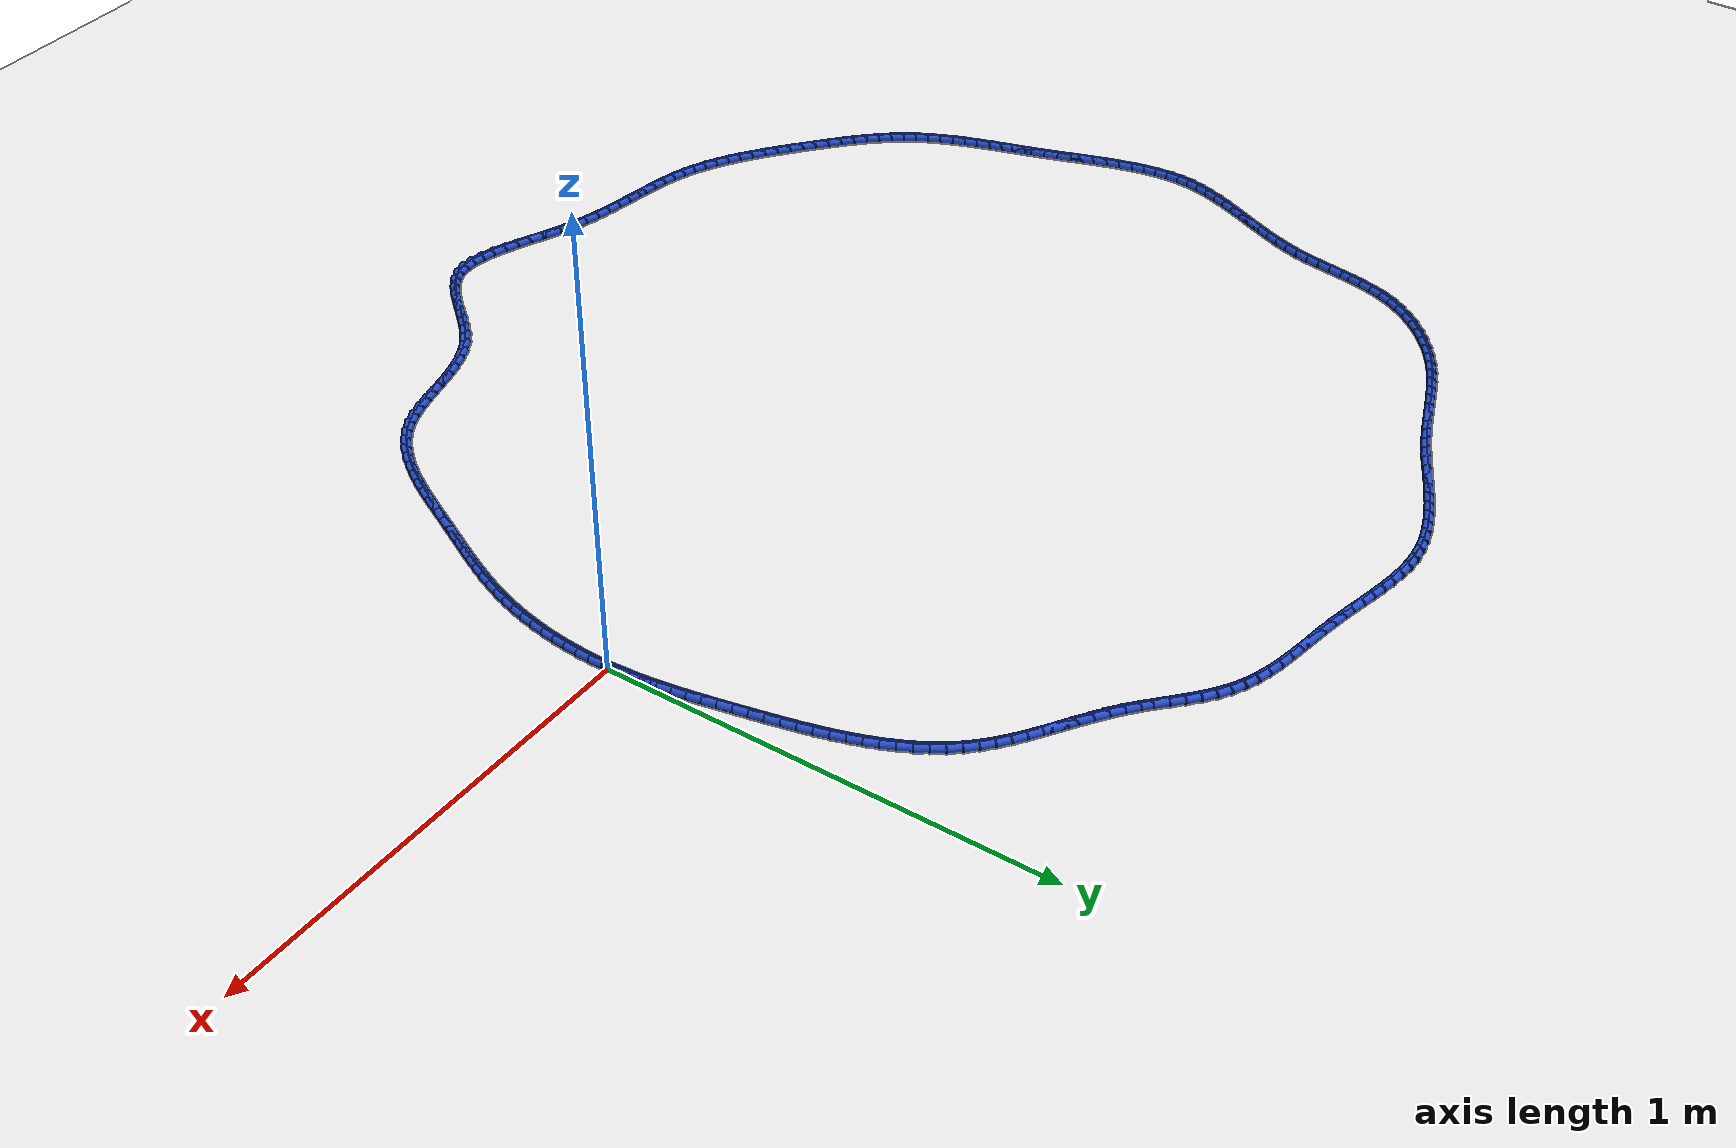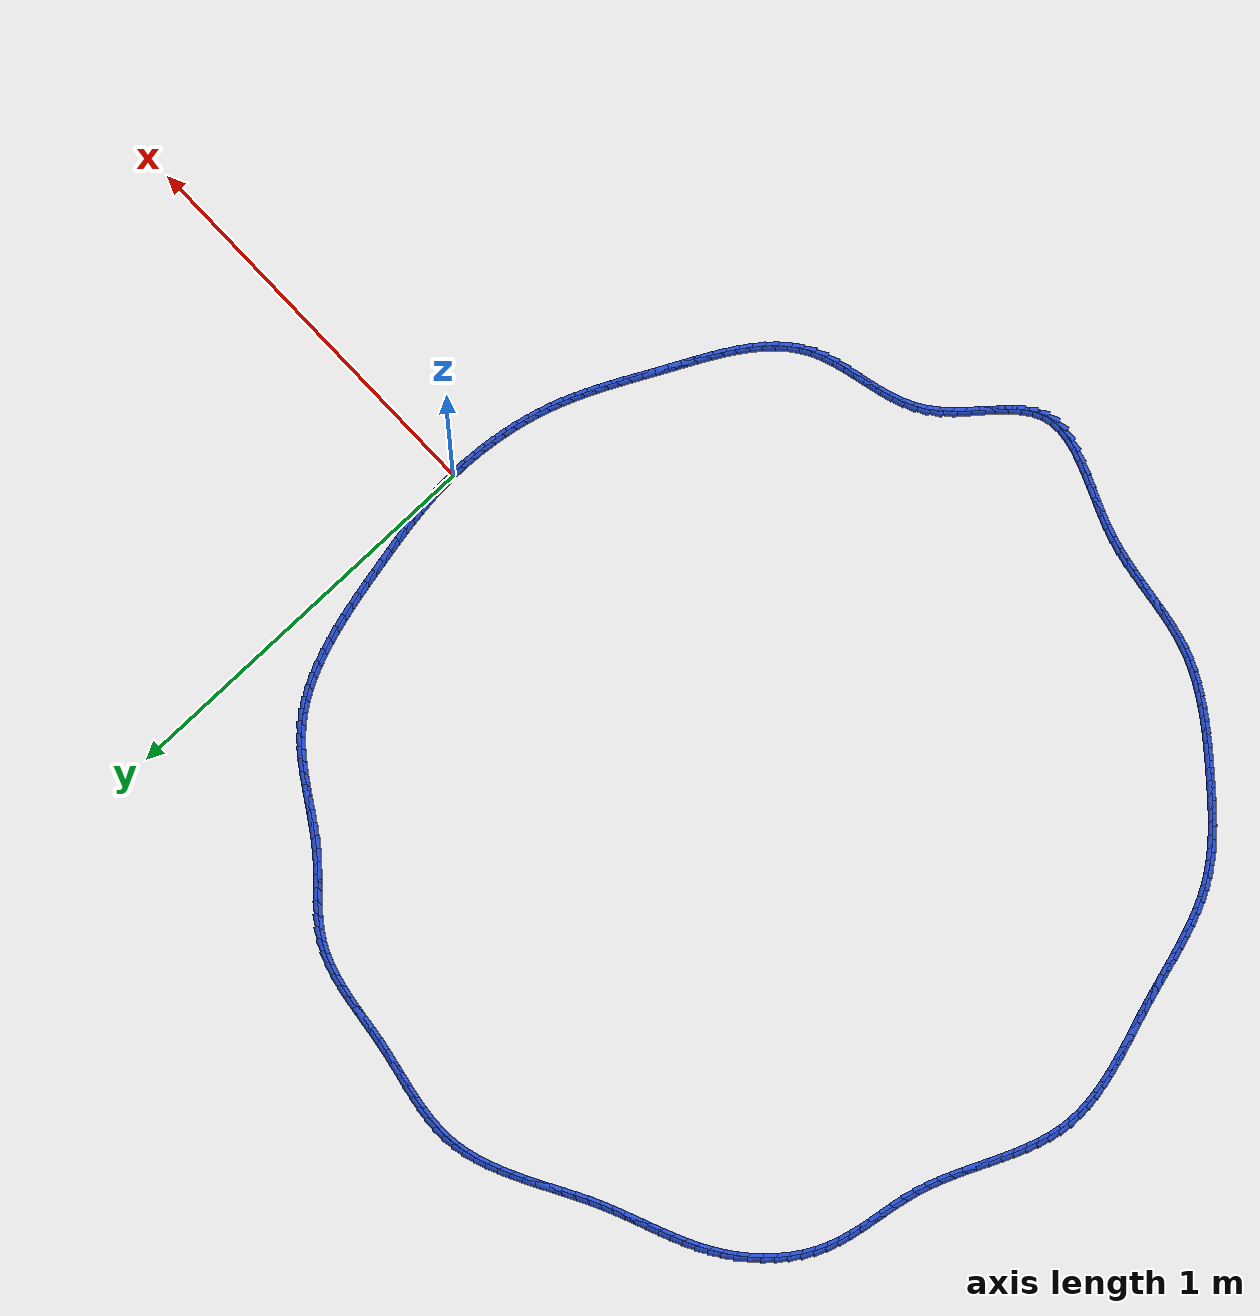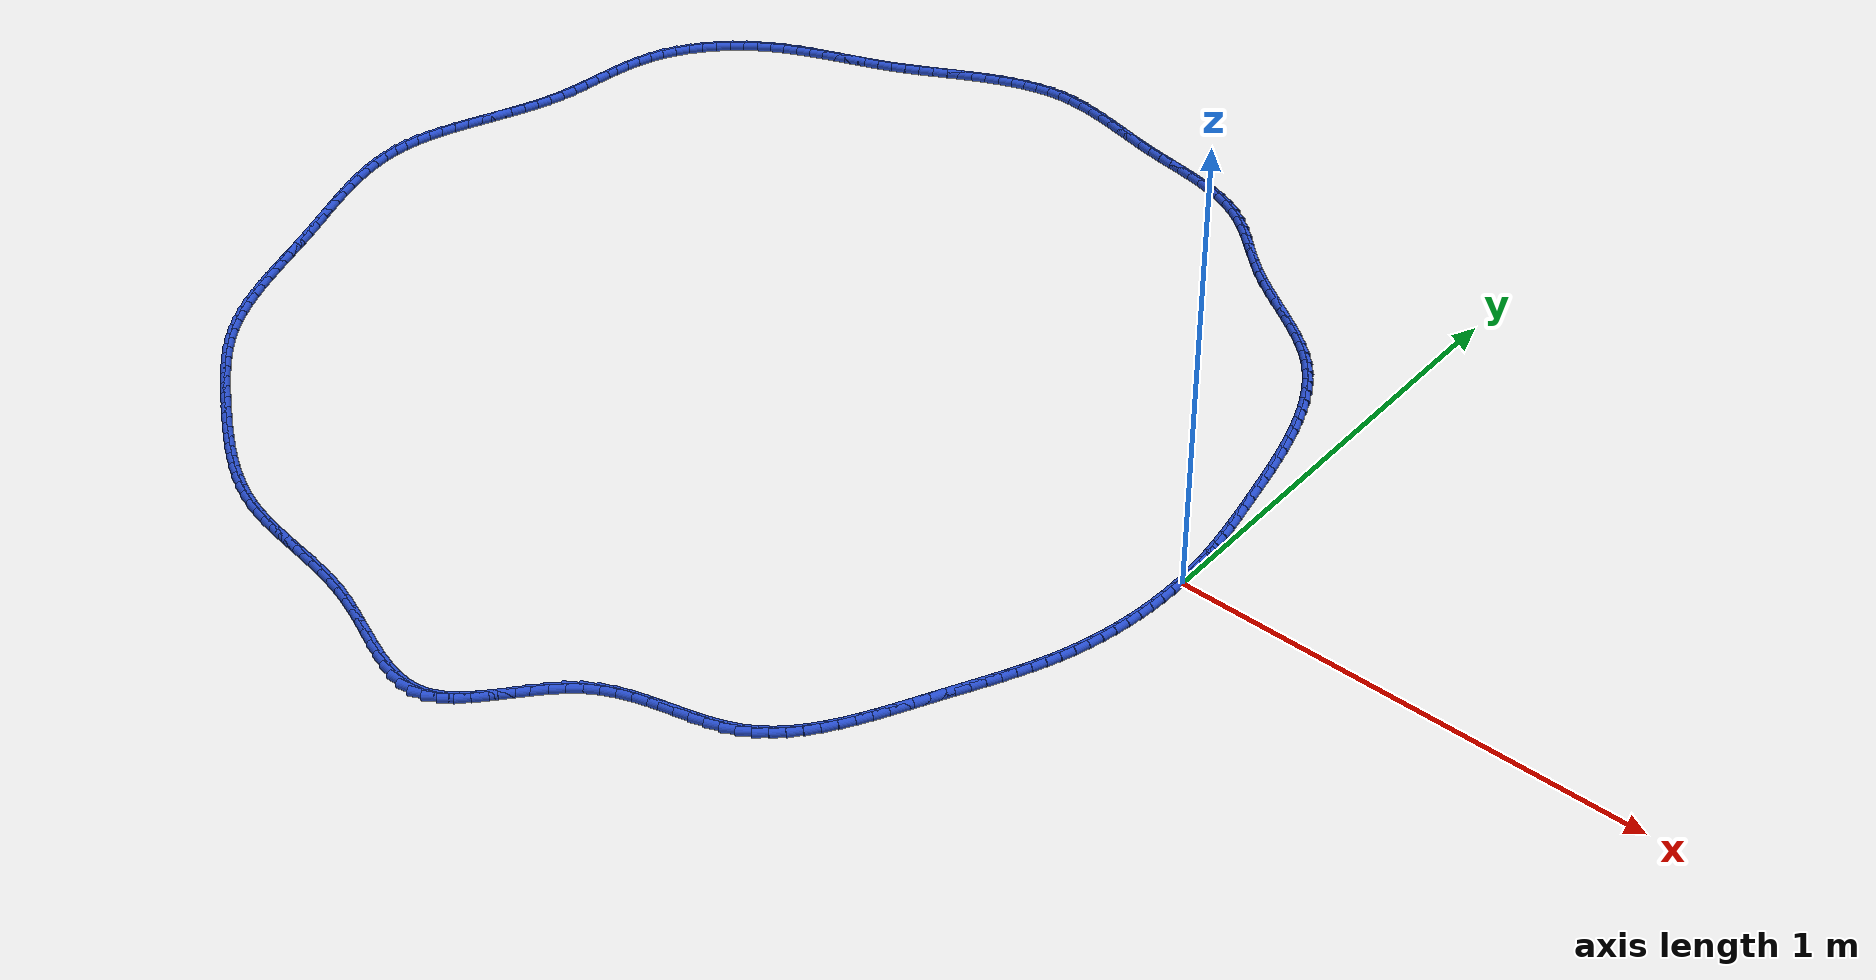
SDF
<sdf version="1.6">
 <world name="default">
  <light name="sun" type="directional">
   <pose>0 0 10 0 -0 0</pose>
   <diffuse>0.8 0.8 0.8 1</diffuse>
   <specular>0.2 0.2 0.2 1</specular>
   <attenuation>
    <range>1000</range>
    <constant>0.9</constant>
    <linear>0.01</linear>
    <quadratic>0.001</quadratic>
   </attenuation>
   <direction>-0.5 0.1 -0.9</direction>
  </light>
  <model name="ground_plane">
   <static>1</static>
   <link name="link">
    <collision name="collision">
     <geometry><plane><normal>0 0 1</normal><size>100 100</size></plane></geometry>
     <surface><friction><ode><mu>100</mu><mu2>50</mu2></ode></friction></surface>
    </collision>
    <visual name="visual">
     <cast_shadows>0</cast_shadows>
     <geometry><plane><normal>0 0 1</normal><size>100 100</size></plane></geometry>
     <material>
      <script><uri>file://media/materials/scripts/gazebo.material</uri><name>Gazebo/WhiteGlow</name></script>
     </material>
    </visual>
   </link>
  </model>
  <gravity>0 0 -9.8</gravity>
  <magnetic_field>6e-06 2.3e-05 -4.2e-05</magnetic_field>
  <atmosphere type="adiabatic"/>
  <physics name="default_physics" default="0" type="ode">
   <max_step_size>0.001</max_step_size>
   <real_time_factor>1</real_time_factor>
   <real_time_update_rate>1000</real_time_update_rate>
  </physics>
  <scene><ambient>0.4 0.4 0.4 1</ambient><background>0.7 0.7 0.7 1</background><shadows>1</shadows></scene>
  <spherical_coordinates>
   <surface_model>EARTH_WGS84</surface_model>
   <latitude_deg>0</latitude_deg>
   <longitude_deg>0</longitude_deg>
   <elevation>0</elevation>
   <heading_deg>0</heading_deg>
  </spherical_coordinates>
  <model name="line">
   <link name="link_0">
    <pose>-1.9949319973733282e-17 5.551115123125783e-17 0.01 0 1.57 -1.5289653326839188</pose>
    <collision name="collision">
     <geometry><cylinder><radius>0.01</radius><length>0.08</length></cylinder></geometry>
    </collision>
    <visual name="visual">
     <material>
      <script><name>Gazebo/Blue</name><uri>file://media/materials/scripts/gazebo.material</uri></script>
     </material>
     <geometry><cylinder><radius>0.01</radius><length>0.08</length></cylinder></geometry>
    </visual>
   </link>
   <link name="link_1">
    <pose>-0.0012793142125460944 0.030565085952302996 0.01 0 1.57 -1.4955938856073712</pose>
    <collision name="collision">
     <geometry><cylinder><radius>0.01</radius><length>0.08</length></cylinder></geometry>
    </collision>
    <visual name="visual">
     <material>
      <script><name>Gazebo/Blue</name><uri>file://media/materials/scripts/gazebo.material</uri></script>
     </material>
     <geometry><cylinder><radius>0.01</radius><length>0.08</length></cylinder></geometry>
    </visual>
   </link>
   <link name="link_2">
    <pose>-0.003569841791417455 0.06096580112256882 0.01 0 1.57 -1.4657438496458983</pose>
    <collision name="collision">
     <geometry><cylinder><radius>0.01</radius><length>0.08</length></cylinder></geometry>
    </collision>
    <visual name="visual">
     <material>
      <script><name>Gazebo/Blue</name><uri>file://media/materials/scripts/gazebo.material</uri></script>
     </material>
     <geometry><cylinder><radius>0.01</radius><length>0.08</length></cylinder></geometry>
    </visual>
   </link>
   <link name="link_3">
    <pose>-0.006763926267108752 0.09125852635424452 0.01 0 1.57 -1.4396149479589366</pose>
    <collision name="collision">
     <geometry><cylinder><radius>0.01</radius><length>0.08</length></cylinder></geometry>
    </collision>
    <visual name="visual">
     <material>
      <script><name>Gazebo/Blue</name><uri>file://media/materials/scripts/gazebo.material</uri></script>
     </material>
     <geometry><cylinder><radius>0.01</radius><length>0.08</length></cylinder></geometry>
    </visual>
   </link>
   <link name="link_4">
    <pose>-0.010753911170114629 0.12149964249077708 0.01 0 1.57 -1.417339156078249</pose>
    <collision name="collision">
     <geometry><cylinder><radius>0.01</radius><length>0.08</length></cylinder></geometry>
    </collision>
    <visual name="visual">
     <material>
      <script><name>Gazebo/Blue</name><uri>file://media/materials/scripts/gazebo.material</uri></script>
     </material>
     <geometry><cylinder><radius>0.01</radius><length>0.08</length></cylinder></geometry>
    </visual>
   </link>
   <link name="link_5">
    <pose>-0.015432140030929735 0.15174553037561347 0.01 0 1.57 -1.3989890061283723</pose>
    <collision name="collision">
     <geometry><cylinder><radius>0.01</radius><length>0.08</length></cylinder></geometry>
    </collision>
    <visual name="visual">
     <material>
      <script><name>Gazebo/Blue</name><uri>file://media/materials/scripts/gazebo.material</uri></script>
     </material>
     <geometry><cylinder><radius>0.01</radius><length>0.08</length></cylinder></geometry>
    </visual>
   </link>
   <link name="link_6">
    <pose>-0.02069095638004872 0.18205257085220064 0.01 0 1.57 -1.3845867775588265</pose>
    <collision name="collision">
     <geometry><cylinder><radius>0.01</radius><length>0.08</length></cylinder></geometry>
    </collision>
    <visual name="visual">
     <material>
      <script><name>Gazebo/Blue</name><uri>file://media/materials/scripts/gazebo.material</uri></script>
     </material>
     <geometry><cylinder><radius>0.01</radius><length>0.08</length></cylinder></geometry>
    </visual>
   </link>
   <link name="link_7">
    <pose>-0.02642270374796623 0.21247714476398566 0.01 0 1.57 -1.3741134388161529</pose>
    <collision name="collision">
     <geometry><cylinder><radius>0.01</radius><length>0.08</length></cylinder></geometry>
    </collision>
    <visual name="visual">
     <material>
      <script><name>Gazebo/Blue</name><uri>file://media/materials/scripts/gazebo.material</uri></script>
     </material>
     <geometry><cylinder><radius>0.01</radius><length>0.08</length></cylinder></geometry>
    </visual>
   </link>
   <link name="link_8">
    <pose>-0.03251972566517692 0.24307563295441545 0.01 0 1.57 -1.3675165659097024</pose>
    <collision name="collision">
     <geometry><cylinder><radius>0.01</radius><length>0.08</length></cylinder></geometry>
    </collision>
    <visual name="visual">
     <material>
      <script><name>Gazebo/Blue</name><uri>file://media/materials/scripts/gazebo.material</uri></script>
     </material>
     <geometry><cylinder><radius>0.01</radius><length>0.08</length></cylinder></geometry>
    </visual>
   </link>
   <link name="link_9">
    <pose>-0.03887436566217543 0.27390441626693696 0.01 0 1.57 -1.36413426950641</pose>
    <collision name="collision">
     <geometry><cylinder><radius>0.01</radius><length>0.08</length></cylinder></geometry>
    </collision>
    <visual name="visual">
     <material>
      <script><name>Gazebo/Blue</name><uri>file://media/materials/scripts/gazebo.material</uri></script>
     </material>
     <geometry><cylinder><radius>0.01</radius><length>0.08</length></cylinder></geometry>
    </visual>
   </link>
   <link name="link_10">
    <pose>-0.045395032133502045 0.30500625630234757 0.01 0 1.57 -1.35880597664031</pose>
    <collision name="collision">
     <geometry><cylinder><radius>0.01</radius><length>0.08</length></cylinder></geometry>
    </collision>
    <visual name="visual">
     <material>
      <script><name>Gazebo/Blue</name><uri>file://media/materials/scripts/gazebo.material</uri></script>
     </material>
     <geometry><cylinder><radius>0.01</radius><length>0.08</length></cylinder></geometry>
    </visual>
   </link>
   <link name="link_11">
    <pose>-0.05213114120278557 0.33630437312829115 0.01 0 1.57 -1.348903417357576</pose>
    <collision name="collision">
     <geometry><cylinder><radius>0.01</radius><length>0.08</length></cylinder></geometry>
    </collision>
    <visual name="visual">
     <material>
      <script><name>Gazebo/Blue</name><uri>file://media/materials/scripts/gazebo.material</uri></script>
     </material>
     <geometry><cylinder><radius>0.01</radius><length>0.08</length></cylinder></geometry>
    </visual>
   </link>
   <link name="link_12">
    <pose>-0.05920521788855795 0.3676600075901353 0.01 0 1.57 -1.3343608256101234</pose>
    <collision name="collision">
     <geometry><cylinder><radius>0.01</radius><length>0.08</length></cylinder></geometry>
    </collision>
    <visual name="visual">
     <material>
      <script><name>Gazebo/Blue</name><uri>file://media/materials/scripts/gazebo.material</uri></script>
     </material>
     <geometry><cylinder><radius>0.01</radius><length>0.08</length></cylinder></geometry>
    </visual>
   </link>
   <link name="link_13">
    <pose>-0.06674040664647819 0.39893387539562275 0.01 0 1.57 -1.3150498745148993</pose>
    <collision name="collision">
     <geometry><cylinder><radius>0.01</radius><length>0.08</length></cylinder></geometry>
    </collision>
    <visual name="visual">
     <material>
      <script><name>Gazebo/Blue</name><uri>file://media/materials/scripts/gazebo.material</uri></script>
     </material>
     <geometry><cylinder><radius>0.01</radius><length>0.08</length></cylinder></geometry>
    </visual>
   </link>
   <link name="link_14">
    <pose>-0.07485985193220533 0.4299866922524965 0.01 0 1.57 -1.290763513359447</pose>
    <collision name="collision">
     <geometry><cylinder><radius>0.01</radius><length>0.08</length></cylinder></geometry>
    </collision>
    <visual name="visual">
     <material>
      <script><name>Gazebo/Blue</name><uri>file://media/materials/scripts/gazebo.material</uri></script>
     </material>
     <geometry><cylinder><radius>0.01</radius><length>0.08</length></cylinder></geometry>
    </visual>
   </link>
   <link name="link_15">
    <pose>-0.08368669820139843 0.4606791738684998 0.01 0 1.57 -1.2612233022906032</pose>
    <collision name="collision">
     <geometry><cylinder><radius>0.01</radius><length>0.08</length></cylinder></geometry>
    </collision>
    <visual name="visual">
     <material>
      <script><name>Gazebo/Blue</name><uri>file://media/materials/scripts/gazebo.material</uri></script>
     </material>
     <geometry><cylinder><radius>0.01</radius><length>0.08</length></cylinder></geometry>
    </visual>
   </link>
   <link name="link_16">
    <pose>-0.09334408990971652 0.4908720359513756 0.01 0 1.57 -1.2260900123261078</pose>
    <collision name="collision">
     <geometry><cylinder><radius>0.01</radius><length>0.08</length></cylinder></geometry>
    </collision>
    <visual name="visual">
     <material>
      <script><name>Gazebo/Blue</name><uri>file://media/materials/scripts/gazebo.material</uri></script>
     </material>
     <geometry><cylinder><radius>0.01</radius><length>0.08</length></cylinder></geometry>
    </visual>
   </link>
   <link name="link_17">
    <pose>-0.1039551715128186 0.5204259942088669 0.01 0 1.57 -1.1849804950862828</pose>
    <collision name="collision">
     <geometry><cylinder><radius>0.01</radius><length>0.08</length></cylinder></geometry>
    </collision>
    <visual name="visual">
     <material>
      <script><name>Gazebo/Blue</name><uri>file://media/materials/scripts/gazebo.material</uri></script>
     </material>
     <geometry><cylinder><radius>0.01</radius><length>0.08</length></cylinder></geometry>
    </visual>
   </link>
   <link name="link_18">
    <pose>-0.11564308746636379 0.5492017643487167 0.01 0 1.57 -1.1374946750342765</pose>
    <collision name="collision">
     <geometry><cylinder><radius>0.01</radius><length>0.08</length></cylinder></geometry>
    </collision>
    <visual name="visual">
     <material>
      <script><name>Gazebo/Blue</name><uri>file://media/materials/scripts/gazebo.material</uri></script>
     </material>
     <geometry><cylinder><radius>0.01</radius><length>0.08</length></cylinder></geometry>
    </visual>
   </link>
   <link name="link_19">
    <pose>-0.12853098222601106 0.577060062078668 0.01 0 1.57 -1.0832571278311915</pose>
    <collision name="collision">
     <geometry><cylinder><radius>0.01</radius><length>0.08</length></cylinder></geometry>
    </collision>
    <visual name="visual">
     <material>
      <script><name>Gazebo/Blue</name><uri>file://media/materials/scripts/gazebo.material</uri></script>
     </material>
     <geometry><cylinder><radius>0.01</radius><length>0.08</length></cylinder></geometry>
    </visual>
   </link>
   <link name="link_20">
    <pose>-0.14274200024741943 0.6038616031064638 0.01 0 1.57 -1.021977401247454</pose>
    <collision name="collision">
     <geometry><cylinder><radius>0.01</radius><length>0.08</length></cylinder></geometry>
    </collision>
    <visual name="visual">
     <material>
      <script><name>Gazebo/Blue</name><uri>file://media/materials/scripts/gazebo.material</uri></script>
     </material>
     <geometry><cylinder><radius>0.01</radius><length>0.08</length></cylinder></geometry>
    </visual>
   </link>
   <link name="link_21">
    <pose>-0.15839928598624795 0.6294671031398471 0.01 0 1.57 -0.9535308733855988</pose>
    <collision name="collision">
     <geometry><cylinder><radius>0.01</radius><length>0.08</length></cylinder></geometry>
    </collision>
    <visual name="visual">
     <material>
      <script><name>Gazebo/Blue</name><uri>file://media/materials/scripts/gazebo.material</uri></script>
     </material>
     <geometry><cylinder><radius>0.01</radius><length>0.08</length></cylinder></geometry>
    </visual>
   </link>
   <link name="link_22">
    <pose>-0.17562598389815565 0.653737277886561 0.01 0 1.57 -0.8780561430552011</pose>
    <collision name="collision">
     <geometry><cylinder><radius>0.01</radius><length>0.08</length></cylinder></geometry>
    </collision>
    <visual name="visual">
     <material>
      <script><name>Gazebo/Blue</name><uri>file://media/materials/scripts/gazebo.material</uri></script>
     </material>
     <geometry><cylinder><radius>0.01</radius><length>0.08</length></cylinder></geometry>
    </visual>
   </link>
   <link name="link_23">
    <pose>-0.19454523843880167 0.6765328430543487 0.01 0 1.57 -0.797303130862807</pose>
    <collision name="collision">
     <geometry><cylinder><radius>0.01</radius><length>0.08</length></cylinder></geometry>
    </collision>
    <visual name="visual">
     <material>
      <script><name>Gazebo/Blue</name><uri>file://media/materials/scripts/gazebo.material</uri></script>
     </material>
     <geometry><cylinder><radius>0.01</radius><length>0.08</length></cylinder></geometry>
    </visual>
   </link>
   <link name="link_24">
    <pose>-0.21525478350491845 0.6977414458844622 0.01 0 1.57 -0.7241617399569318</pose>
    <collision name="collision">
     <geometry><cylinder><radius>0.01</radius><length>0.08</length></cylinder></geometry>
    </collision>
    <visual name="visual">
     <material>
      <script><name>Gazebo/Blue</name><uri>file://media/materials/scripts/gazebo.material</uri></script>
     </material>
     <geometry><cylinder><radius>0.01</radius><length>0.08</length></cylinder></geometry>
    </visual>
   </link>
   <link name="link_25">
    <pose>-0.2376068602889616 0.7175109205353584 0.01 0 1.57 -0.6658429942838564</pose>
    <collision name="collision">
     <geometry><cylinder><radius>0.01</radius><length>0.08</length></cylinder></geometry>
    </collision>
    <visual name="visual">
     <material>
      <script><name>Gazebo/Blue</name><uri>file://media/materials/scripts/gazebo.material</uri></script>
     </material>
     <geometry><cylinder><radius>0.01</radius><length>0.08</length></cylinder></geometry>
    </visual>
   </link>
   <link name="link_26">
    <pose>-0.26131619727023786 0.7361348448405092 0.01 0 1.57 -0.62221585230723</pose>
    <collision name="collision">
     <geometry><cylinder><radius>0.01</radius><length>0.08</length></cylinder></geometry>
    </collision>
    <visual name="visual">
     <material>
      <script><name>Gazebo/Blue</name><uri>file://media/materials/scripts/gazebo.material</uri></script>
     </material>
     <geometry><cylinder><radius>0.01</radius><length>0.08</length></cylinder></geometry>
    </visual>
   </link>
   <link name="link_27">
    <pose>-0.28609600941314794 0.7539084007412504 0.01 0 1.57 -0.5927548116707138</pose>
    <collision name="collision">
     <geometry><cylinder><radius>0.01</radius><length>0.08</length></cylinder></geometry>
    </collision>
    <visual name="visual">
     <material>
      <script><name>Gazebo/Blue</name><uri>file://media/materials/scripts/gazebo.material</uri></script>
     </material>
     <geometry><cylinder><radius>0.01</radius><length>0.08</length></cylinder></geometry>
    </visual>
   </link>
   <link name="link_28">
    <pose>-0.31165951168209255 0.7711267701789181 0.01 0 1.57 -0.5768902801380734</pose>
    <collision name="collision">
     <geometry><cylinder><radius>0.01</radius><length>0.08</length></cylinder></geometry>
    </collision>
    <visual name="visual">
     <material>
      <script><name>Gazebo/Blue</name><uri>file://media/materials/scripts/gazebo.material</uri></script>
     </material>
     <geometry><cylinder><radius>0.01</radius><length>0.08</length></cylinder></geometry>
    </visual>
   </link>
   <link name="link_29">
    <pose>-0.3377199190414727 0.7880851350948477 0.01 0 1.57 -0.5741697424420177</pose>
    <collision name="collision">
     <geometry><cylinder><radius>0.01</radius><length>0.08</length></cylinder></geometry>
    </collision>
    <visual name="visual">
     <material>
      <script><name>Gazebo/Blue</name><uri>file://media/materials/scripts/gazebo.material</uri></script>
     </material>
     <geometry><cylinder><radius>0.01</radius><length>0.08</length></cylinder></geometry>
    </visual>
   </link>
   <link name="link_30">
    <pose>-0.3639904464556889 0.8050786774303752 0.01 0 1.57 -0.5843284876399779</pose>
    <collision name="collision">
     <geometry><cylinder><radius>0.01</radius><length>0.08</length></cylinder></geometry>
    </collision>
    <visual name="visual">
     <material>
      <script><name>Gazebo/Blue</name><uri>file://media/materials/scripts/gazebo.material</uri></script>
     </material>
     <geometry><cylinder><radius>0.01</radius><length>0.08</length></cylinder></geometry>
    </visual>
   </link>
   <link name="link_31">
    <pose>-0.39018430888914224 0.8224025791268366 0.01 0 1.57 -0.607292051179603</pose>
    <collision name="collision">
     <geometry><cylinder><radius>0.01</radius><length>0.08</length></cylinder></geometry>
    </collision>
    <visual name="visual">
     <material>
      <script><name>Gazebo/Blue</name><uri>file://media/materials/scripts/gazebo.material</uri></script>
     </material>
     <geometry><cylinder><radius>0.01</radius><length>0.08</length></cylinder></geometry>
    </visual>
   </link>
   <link name="link_32">
    <pose>-0.4160147213062331 0.8403520221255674 0.01 0 1.57 -0.6431205922775654</pose>
    <collision name="collision">
     <geometry><cylinder><radius>0.01</radius><length>0.08</length></cylinder></geometry>
    </collision>
    <visual name="visual">
     <material>
      <script><name>Gazebo/Blue</name><uri>file://media/materials/scripts/gazebo.material</uri></script>
     </material>
     <geometry><cylinder><radius>0.01</radius><length>0.08</length></cylinder></geometry>
    </visual>
   </link>
   <link name="link_33">
    <pose>-0.44119489867136275 0.8592221883679039 0.01 0 1.57 -0.689900159431687</pose>
    <collision name="collision">
     <geometry><cylinder><radius>0.01</radius><length>0.08</length></cylinder></geometry>
    </collision>
    <visual name="visual">
     <material>
      <script><name>Gazebo/Blue</name><uri>file://media/materials/scripts/gazebo.material</uri></script>
     </material>
     <geometry><cylinder><radius>0.01</radius><length>0.08</length></cylinder></geometry>
    </visual>
   </link>
   <link name="link_34">
    <pose>-0.4654744909637667 0.8792569375158138 0.01 0 1.57 -0.7266518623340765</pose>
    <collision name="collision">
     <geometry><cylinder><radius>0.01</radius><length>0.08</length></cylinder></geometry>
    </collision>
    <visual name="visual">
     <material>
      <script><name>Gazebo/Blue</name><uri>file://media/materials/scripts/gazebo.material</uri></script>
     </material>
     <geometry><cylinder><radius>0.01</radius><length>0.08</length></cylinder></geometry>
    </visual>
   </link>
   <link name="link_35">
    <pose>-0.48898790971873035 0.9001581549749372 0.01 0 1.57 -0.7409505809943913</pose>
    <collision name="collision">
     <geometry><cylinder><radius>0.01</radius><length>0.08</length></cylinder></geometry>
    </collision>
    <visual name="visual">
     <material>
      <script><name>Gazebo/Blue</name><uri>file://media/materials/scripts/gazebo.material</uri></script>
     </material>
     <geometry><cylinder><radius>0.01</radius><length>0.08</length></cylinder></geometry>
    </visual>
   </link>
   <link name="link_36">
    <pose>-0.5121005394377249 0.9213023781539208 0.01 0 1.57 -0.7325039884930652</pose>
    <collision name="collision">
     <geometry><cylinder><radius>0.01</radius><length>0.08</length></cylinder></geometry>
    </collision>
    <visual name="visual">
     <material>
      <script><name>Gazebo/Blue</name><uri>file://media/materials/scripts/gazebo.material</uri></script>
     </material>
     <geometry><cylinder><radius>0.01</radius><length>0.08</length></cylinder></geometry>
    </visual>
   </link>
   <link name="link_37">
    <pose>-0.5351809080485513 0.942061716638204 0.01 0 1.57 -0.7005743832918859</pose>
    <collision name="collision">
     <geometry><cylinder><radius>0.01</radius><length>0.08</length></cylinder></geometry>
    </collision>
    <visual name="visual">
     <material>
      <script><name>Gazebo/Blue</name><uri>file://media/materials/scripts/gazebo.material</uri></script>
     </material>
     <geometry><cylinder><radius>0.01</radius><length>0.08</length></cylinder></geometry>
    </visual>
   </link>
   <link name="link_38">
    <pose>-0.5585975434790101 0.9618082800132266 0.01 0 1.57 -0.6438943417208032</pose>
    <collision name="collision">
     <geometry><cylinder><radius>0.01</radius><length>0.08</length></cylinder></geometry>
    </collision>
    <visual name="visual">
     <material>
      <script><name>Gazebo/Blue</name><uri>file://media/materials/scripts/gazebo.material</uri></script>
     </material>
     <geometry><cylinder><radius>0.01</radius><length>0.08</length></cylinder></geometry>
    </visual>
   </link>
   <link name="link_39">
    <pose>-0.5827189736569023 0.9799141778644277 0.01 0 1.57 -0.5611820949017046</pose>
    <collision name="collision">
     <geometry><cylinder><radius>0.01</radius><length>0.08</length></cylinder></geometry>
    </collision>
    <visual name="visual">
     <material>
      <script><name>Gazebo/Blue</name><uri>file://media/materials/scripts/gazebo.material</uri></script>
     </material>
     <geometry><cylinder><radius>0.01</radius><length>0.08</length></cylinder></geometry>
    </visual>
   </link>
   <link name="link_40">
    <pose>-0.6079137199781708 0.9957515322394921 0.01 0 1.57 -0.45967685903800887</pose>
    <collision name="collision">
     <geometry><cylinder><radius>0.01</radius><length>0.08</length></cylinder></geometry>
    </collision>
    <visual name="visual">
     <material>
      <script><name>Gazebo/Blue</name><uri>file://media/materials/scripts/gazebo.material</uri></script>
     </material>
     <geometry><cylinder><radius>0.01</radius><length>0.08</length></cylinder></geometry>
    </visual>
   </link>
   <link name="link_41">
    <pose>-0.6344481752794612 1.008887318051416 0.01 0 1.57 -0.36731859572606823</pose>
    <collision name="collision">
     <geometry><cylinder><radius>0.01</radius><length>0.08</length></cylinder></geometry>
    </collision>
    <visual name="visual">
     <material>
      <script><name>Gazebo/Blue</name><uri>file://media/materials/scripts/gazebo.material</uri></script>
     </material>
     <geometry><cylinder><radius>0.01</radius><length>0.08</length></cylinder></geometry>
    </visual>
   </link>
   <link name="link_42">
    <pose>-0.6622281200494722 1.0195765288217744 0.01 0 1.57 -0.2912631749124547</pose>
    <collision name="collision">
     <geometry><cylinder><radius>0.01</radius><length>0.08</length></cylinder></geometry>
    </collision>
    <visual name="visual">
     <material>
      <script><name>Gazebo/Blue</name><uri>file://media/materials/scripts/gazebo.material</uri></script>
     </material>
     <geometry><cylinder><radius>0.01</radius><length>0.08</length></cylinder></geometry>
    </visual>
   </link>
   <link name="link_43">
    <pose>-0.6910797817531756 1.0282259386781156 0.01 0 1.57 -0.23161536392953921</pose>
    <collision name="collision">
     <geometry><cylinder><radius>0.01</radius><length>0.08</length></cylinder></geometry>
    </collision>
    <visual name="visual">
     <material>
      <script><name>Gazebo/Blue</name><uri>file://media/materials/scripts/gazebo.material</uri></script>
     </material>
     <geometry><cylinder><radius>0.01</radius><length>0.08</length></cylinder></geometry>
    </visual>
   </link>
   <link name="link_44">
    <pose>-0.7208293878555434 1.0352423217479876 0.01 0 1.57 -0.1877655126679093</pose>
    <collision name="collision">
     <geometry><cylinder><radius>0.01</radius><length>0.08</length></cylinder></geometry>
    </collision>
    <visual name="visual">
     <material>
      <script><name>Gazebo/Blue</name><uri>file://media/materials/scripts/gazebo.material</uri></script>
     </material>
     <geometry><cylinder><radius>0.01</radius><length>0.08</length></cylinder></geometry>
    </visual>
   </link>
   <link name="link_45">
    <pose>-0.751303165821547 1.0410324521589378 0.01 0 1.57 -0.15886844957968024</pose>
    <collision name="collision">
     <geometry><cylinder><radius>0.01</radius><length>0.08</length></cylinder></geometry>
    </collision>
    <visual name="visual">
     <material>
      <script><name>Gazebo/Blue</name><uri>file://media/materials/scripts/gazebo.material</uri></script>
     </material>
     <geometry><cylinder><radius>0.01</radius><length>0.08</length></cylinder></geometry>
    </visual>
   </link>
   <link name="link_46">
    <pose>-0.7823273431161581 1.0460031040385152 0.01 0 1.57 -0.14414709625055966</pose>
    <collision name="collision">
     <geometry><cylinder><radius>0.01</radius><length>0.08</length></cylinder></geometry>
    </collision>
    <visual name="visual">
     <material>
      <script><name>Gazebo/Blue</name><uri>file://media/materials/scripts/gazebo.material</uri></script>
     </material>
     <geometry><cylinder><radius>0.01</radius><length>0.08</length></cylinder></geometry>
    </visual>
   </link>
   <link name="link_47">
    <pose>-0.8137281472043489 1.0505610515142672 0.01 0 1.57 -0.14305067615243347</pose>
    <collision name="collision">
     <geometry><cylinder><radius>0.01</radius><length>0.08</length></cylinder></geometry>
    </collision>
    <visual name="visual">
     <material>
      <script><name>Gazebo/Blue</name><uri>file://media/materials/scripts/gazebo.material</uri></script>
     </material>
     <geometry><cylinder><radius>0.01</radius><length>0.08</length></cylinder></geometry>
    </visual>
   </link>
   <link name="link_48">
    <pose>-0.8453318055510912 1.0551130687137424 0.01 0 1.57 -0.1553128937771225</pose>
    <collision name="collision">
     <geometry><cylinder><radius>0.01</radius><length>0.08</length></cylinder></geometry>
    </collision>
    <visual name="visual">
     <material>
      <script><name>Gazebo/Blue</name><uri>file://media/materials/scripts/gazebo.material</uri></script>
     </material>
     <geometry><cylinder><radius>0.01</radius><length>0.08</length></cylinder></geometry>
    </visual>
   </link>
   <link name="link_49">
    <pose>-0.8769645456213562 1.0600659297644883 0.01 0 1.57 -0.17925850150893474</pose>
    <collision name="collision">
     <geometry><cylinder><radius>0.01</radius><length>0.08</length></cylinder></geometry>
    </collision>
    <visual name="visual">
     <material>
      <script><name>Gazebo/Blue</name><uri>file://media/materials/scripts/gazebo.material</uri></script>
     </material>
     <geometry><cylinder><radius>0.01</radius><length>0.08</length></cylinder></geometry>
    </visual>
   </link>
   <link name="link_50">
    <pose>-0.9084627931063454 1.0657735249909477 0.01 0 1.57 -0.19931838487703935</pose>
    <collision name="collision">
     <geometry><cylinder><radius>0.01</radius><length>0.08</length></cylinder></geometry>
    </collision>
    <visual name="visual">
     <material>
      <script><name>Gazebo/Blue</name><uri>file://media/materials/scripts/gazebo.material</uri></script>
     </material>
     <geometry><cylinder><radius>0.01</radius><length>0.08</length></cylinder></geometry>
    </visual>
   </link>
   <link name="link_51">
    <pose>-0.9397583349719058 1.0720952404028772 0.01 0 1.57 -0.20696854054746447</pose>
    <collision name="collision">
     <geometry><cylinder><radius>0.01</radius><length>0.08</length></cylinder></geometry>
    </collision>
    <visual name="visual">
     <material>
      <script><name>Gazebo/Blue</name><uri>file://media/materials/scripts/gazebo.material</uri></script>
     </material>
     <geometry><cylinder><radius>0.01</radius><length>0.08</length></cylinder></geometry>
    </visual>
   </link>
   <link name="link_52">
    <pose>-0.9708350040785989 1.0786205734248349 0.01 0 1.57 -0.20198318390520156</pose>
    <collision name="collision">
     <geometry><cylinder><radius>0.01</radius><length>0.08</length></cylinder></geometry>
    </collision>
    <visual name="visual">
     <material>
      <script><name>Gazebo/Blue</name><uri>file://media/materials/scripts/gazebo.material</uri></script>
     </material>
     <geometry><cylinder><radius>0.01</radius><length>0.08</length></cylinder></geometry>
    </visual>
   </link>
   <link name="link_53">
    <pose>-1.0016771595318588 1.0849362925920887 0.01 0 1.57 -0.1839857550346639</pose>
    <collision name="collision">
     <geometry><cylinder><radius>0.01</radius><length>0.08</length></cylinder></geometry>
    </collision>
    <visual name="visual">
     <material>
      <script><name>Gazebo/Blue</name><uri>file://media/materials/scripts/gazebo.material</uri></script>
     </material>
     <geometry><cylinder><radius>0.01</radius><length>0.08</length></cylinder></geometry>
    </visual>
   </link>
   <link name="link_54">
    <pose>-1.032269160437122 1.0906291664399068 0.01 0 1.57 -0.15236671684889933</pose>
    <collision name="collision">
     <geometry><cylinder><radius>0.01</radius><length>0.08</length></cylinder></geometry>
    </collision>
    <visual name="visual">
     <material>
      <script><name>Gazebo/Blue</name><uri>file://media/materials/scripts/gazebo.material</uri></script>
     </material>
     <geometry><cylinder><radius>0.01</radius><length>0.08</length></cylinder></geometry>
    </visual>
   </link>
   <link name="link_55">
    <pose>-1.0625953658998235 1.095285963503557 0.01 0 1.57 -0.1063541593061356</pose>
    <collision name="collision">
     <geometry><cylinder><radius>0.01</radius><length>0.08</length></cylinder></geometry>
    </collision>
    <visual name="visual">
     <material>
      <script><name>Gazebo/Blue</name><uri>file://media/materials/scripts/gazebo.material</uri></script>
     </material>
     <geometry><cylinder><radius>0.01</radius><length>0.08</length></cylinder></geometry>
    </visual>
   </link>
   <link name="link_56">
    <pose>-1.0926401350253978 1.0984934523183065 0.01 0 1.57 -0.045181112483734014</pose>
    <collision name="collision">
     <geometry><cylinder><radius>0.01</radius><length>0.08</length></cylinder></geometry>
    </collision>
    <visual name="visual">
     <material>
      <script><name>Gazebo/Blue</name><uri>file://media/materials/scripts/gazebo.material</uri></script>
     </material>
     <geometry><cylinder><radius>0.01</radius><length>0.08</length></cylinder></geometry>
    </visual>
   </link>
   <link name="link_57">
    <pose>-1.1223878269192817 1.0998384014194242 0.01 0 1.57 0.031612461838247695</pose>
    <collision name="collision">
     <geometry><cylinder><radius>0.01</radius><length>0.08</length></cylinder></geometry>
    </collision>
    <visual name="visual">
     <material>
      <script><name>Gazebo/Blue</name><uri>file://media/materials/scripts/gazebo.material</uri></script>
     </material>
     <geometry><cylinder><radius>0.01</radius><length>0.08</length></cylinder></geometry>
    </visual>
   </link>
   <link name="link_58">
    <pose>-1.1518228006869096 1.0989075793421779 0.01 0 1.57 0.12149935102310915</pose>
    <collision name="collision">
     <geometry><cylinder><radius>0.01</radius><length>0.08</length></cylinder></geometry>
    </collision>
    <visual name="visual">
     <material>
      <script><name>Gazebo/Blue</name><uri>file://media/materials/scripts/gazebo.material</uri></script>
     </material>
     <geometry><cylinder><radius>0.01</radius><length>0.08</length></cylinder></geometry>
    </visual>
   </link>
   <link name="link_59">
    <pose>-1.1809347986956515 1.0953529821418946 0.01 0 1.57 0.2076296452427021</pose>
    <collision name="collision">
     <geometry><cylinder><radius>0.01</radius><length>0.08</length></cylinder></geometry>
    </collision>
    <visual name="visual">
     <material>
      <script><name>Gazebo/Blue</name><uri>file://media/materials/scripts/gazebo.material</uri></script>
     </material>
     <geometry><cylinder><radius>0.01</radius><length>0.08</length></cylinder></geometry>
    </visual>
   </link>
   <link name="link_60">
    <pose>-1.2097511770273859 1.0892823610178235 0.01 0 1.57 0.2822857974553673</pose>
    <collision name="collision">
     <geometry><cylinder><radius>0.01</radius><length>0.08</length></cylinder></geometry>
    </collision>
    <visual name="visual">
     <material>
      <script><name>Gazebo/Blue</name><uri>file://media/materials/scripts/gazebo.material</uri></script>
     </material>
     <geometry><cylinder><radius>0.01</radius><length>0.08</length></cylinder></geometry>
    </visual>
   </link>
   <link name="link_61">
    <pose>-1.238315336436125 1.080997876095636 0.01 0 1.57 0.34516588704980283</pose>
    <collision name="collision">
     <geometry><cylinder><radius>0.01</radius><length>0.08</length></cylinder></geometry>
    </collision>
    <visual name="visual">
     <material>
      <script><name>Gazebo/Blue</name><uri>file://media/materials/scripts/gazebo.material</uri></script>
     </material>
     <geometry><cylinder><radius>0.01</radius><length>0.08</length></cylinder></geometry>
    </visual>
   </link>
   <link name="link_62">
    <pose>-1.266670737465885 1.0708024119602444 0.01 0 1.57 0.3965333552298193</pose>
    <collision name="collision">
     <geometry><cylinder><radius>0.01</radius><length>0.08</length></cylinder></geometry>
    </collision>
    <visual name="visual">
     <material>
      <script><name>Gazebo/Blue</name><uri>file://media/materials/scripts/gazebo.material</uri></script>
     </material>
     <geometry><cylinder><radius>0.01</radius><length>0.08</length></cylinder></geometry>
    </visual>
   </link>
   <link name="link_63">
    <pose>-1.2948608406606836 1.0589988531965588 0.01 0 1.57 0.43692683836007373</pose>
    <collision name="collision">
     <geometry><cylinder><radius>0.01</radius><length>0.08</length></cylinder></geometry>
    </collision>
    <visual name="visual">
     <material>
      <script><name>Gazebo/Blue</name><uri>file://media/materials/scripts/gazebo.material</uri></script>
     </material>
     <geometry><cylinder><radius>0.01</radius><length>0.08</length></cylinder></geometry>
    </visual>
   </link>
   <link name="link_64">
    <pose>-1.3229291065645377 1.0458900843894918 0.01 0 1.57 0.46696185684867314</pose>
    <collision name="collision">
     <geometry><cylinder><radius>0.01</radius><length>0.08</length></cylinder></geometry>
    </collision>
    <visual name="visual">
     <material>
      <script><name>Gazebo/Blue</name><uri>file://media/materials/scripts/gazebo.material</uri></script>
     </material>
     <geometry><cylinder><radius>0.01</radius><length>0.08</length></cylinder></geometry>
    </visual>
   </link>
   <link name="link_65">
    <pose>-1.3509189957214651 1.0317789901239551 0.01 0 1.57 0.4872021601266697</pose>
    <collision name="collision">
     <geometry><cylinder><radius>0.01</radius><length>0.08</length></cylinder></geometry>
    </collision>
    <visual name="visual">
     <material>
      <script><name>Gazebo/Blue</name><uri>file://media/materials/scripts/gazebo.material</uri></script>
     </material>
     <geometry><cylinder><radius>0.01</radius><length>0.08</length></cylinder></geometry>
    </visual>
   </link>
   <link name="link_66">
    <pose>-1.3788739686754834 1.0169684549848592 0.01 0 1.57 0.49808532303377057</pose>
    <collision name="collision">
     <geometry><cylinder><radius>0.01</radius><length>0.08</length></cylinder></geometry>
    </collision>
    <visual name="visual">
     <material>
      <script><name>Gazebo/Blue</name><uri>file://media/materials/scripts/gazebo.material</uri></script>
     </material>
     <geometry><cylinder><radius>0.01</radius><length>0.08</length></cylinder></geometry>
    </visual>
   </link>
   <link name="link_67">
    <pose>-1.4068374859706094 1.001761363557116 0.01 0 1.57 0.49988490824244575</pose>
    <collision name="collision">
     <geometry><cylinder><radius>0.01</radius><length>0.08</length></cylinder></geometry>
    </collision>
    <visual name="visual">
     <material>
      <script><name>Gazebo/Blue</name><uri>file://media/materials/scripts/gazebo.material</uri></script>
     </material>
     <geometry><cylinder><radius>0.01</radius><length>0.08</length></cylinder></geometry>
    </visual>
   </link>
   <link name="link_68">
    <pose>-1.4348530081508613 0.9864606004256372 0.01 0 1.57 0.49269581591064326</pose>
    <collision name="collision">
     <geometry><cylinder><radius>0.01</radius><length>0.08</length></cylinder></geometry>
    </collision>
    <visual name="visual">
     <material>
      <script><name>Gazebo/Blue</name><uri>file://media/materials/scripts/gazebo.material</uri></script>
     </material>
     <geometry><cylinder><radius>0.01</radius><length>0.08</length></cylinder></geometry>
    </visual>
   </link>
   <link name="link_69">
    <pose>-1.4629639957602552 0.9713690501753339 0.01 0 1.57 0.4764353361423157</pose>
    <collision name="collision">
     <geometry><cylinder><radius>0.01</radius><length>0.08</length></cylinder></geometry>
    </collision>
    <visual name="visual">
     <material>
      <script><name>Gazebo/Blue</name><uri>file://media/materials/scripts/gazebo.material</uri></script>
     </material>
     <geometry><cylinder><radius>0.01</radius><length>0.08</length></cylinder></geometry>
    </visual>
   </link>
   <link name="link_70">
    <pose>-1.4912139093428094 0.9567895973911179 0.01 0 1.57 0.4508698298078696</pose>
    <collision name="collision">
     <geometry><cylinder><radius>0.01</radius><length>0.08</length></cylinder></geometry>
    </collision>
    <visual name="visual">
     <material>
      <script><name>Gazebo/Blue</name><uri>file://media/materials/scripts/gazebo.material</uri></script>
     </material>
     <geometry><cylinder><radius>0.01</radius><length>0.08</length></cylinder></geometry>
    </visual>
   </link>
   <link name="link_71">
    <pose>-1.519646119617783 0.9430247593490297 0.01 0 1.57 0.4205344689125636</pose>
    <collision name="collision">
     <geometry><cylinder><radius>0.01</radius><length>0.08</length></cylinder></geometry>
    </collision>
    <visual name="visual">
     <material>
      <script><name>Gazebo/Blue</name><uri>file://media/materials/scripts/gazebo.material</uri></script>
     </material>
     <geometry><cylinder><radius>0.01</radius><length>0.08</length></cylinder></geometry>
    </visual>
   </link>
   <link name="link_72">
    <pose>-1.5482668551595946 0.930225172712064 0.01 0 1.57 0.39781383958420435</pose>
    <collision name="collision">
     <geometry><cylinder><radius>0.01</radius><length>0.08</length></cylinder></geometry>
    </collision>
    <visual name="visual">
     <material>
      <script><name>Gazebo/Blue</name><uri>file://media/materials/scripts/gazebo.material</uri></script>
     </material>
     <geometry><cylinder><radius>0.01</radius><length>0.08</length></cylinder></geometry>
    </visual>
   </link>
   <link name="link_73">
    <pose>-1.5769880729459738 0.9181559813840023 0.01 0 1.57 0.3848910896534666</pose>
    <collision name="collision">
     <geometry><cylinder><radius>0.01</radius><length>0.08</length></cylinder></geometry>
    </collision>
    <visual name="visual">
     <material>
      <script><name>Gazebo/Blue</name><uri>file://media/materials/scripts/gazebo.material</uri></script>
     </material>
     <geometry><cylinder><radius>0.01</radius><length>0.08</length></cylinder></geometry>
    </visual>
   </link>
   <link name="link_74">
    <pose>-1.6057069966420425 0.9065220822214889 0.01 0 1.57 0.3819567492463376</pose>
    <collision name="collision">
     <geometry><cylinder><radius>0.01</radius><length>0.08</length></cylinder></geometry>
    </collision>
    <visual name="visual">
     <material>
      <script><name>Gazebo/Blue</name><uri>file://media/materials/scripts/gazebo.material</uri></script>
     </material>
     <geometry><cylinder><radius>0.01</radius><length>0.08</length></cylinder></geometry>
    </visual>
   </link>
   <link name="link_75">
    <pose>-1.6343208499129243 0.8950283720811695 0.01 0 1.57 0.389162374681091</pose>
    <collision name="collision">
     <geometry><cylinder><radius>0.01</radius><length>0.08</length></cylinder></geometry>
    </collision>
    <visual name="visual">
     <material>
      <script><name>Gazebo/Blue</name><uri>file://media/materials/scripts/gazebo.material</uri></script>
     </material>
     <geometry><cylinder><radius>0.01</radius><length>0.08</length></cylinder></geometry>
    </visual>
   </link>
   <link name="link_76">
    <pose>-1.6627268564237405 0.8833797478196885 0.01 0 1.57 0.40662742229693283</pose>
    <collision name="collision">
     <geometry><cylinder><radius>0.01</radius><length>0.08</length></cylinder></geometry>
    </collision>
    <visual name="visual">
     <material>
      <script><name>Gazebo/Blue</name><uri>file://media/materials/scripts/gazebo.material</uri></script>
     </material>
     <geometry><cylinder><radius>0.01</radius><length>0.08</length></cylinder></geometry>
    </visual>
   </link>
   <link name="link_77">
    <pose>-1.6908222398396135 0.8712811062936915 0.01 0 1.57 0.4344149697003469</pose>
    <collision name="collision">
     <geometry><cylinder><radius>0.01</radius><length>0.08</length></cylinder></geometry>
    </collision>
    <visual name="visual">
     <material>
      <script><name>Gazebo/Blue</name><uri>file://media/materials/scripts/gazebo.material</uri></script>
     </material>
     <geometry><cylinder><radius>0.01</radius><length>0.08</length></cylinder></geometry>
    </visual>
   </link>
   <link name="link_78">
    <pose>-1.7185042238256671 0.8584373443598229 0.01 0 1.57 0.4724747261406459</pose>
    <collision name="collision">
     <geometry><cylinder><radius>0.01</radius><length>0.08</length></cylinder></geometry>
    </collision>
    <visual name="visual">
     <material>
      <script><name>Gazebo/Blue</name><uri>file://media/materials/scripts/gazebo.material</uri></script>
     </material>
     <geometry><cylinder><radius>0.01</radius><length>0.08</length></cylinder></geometry>
    </visual>
   </link>
   <link name="link_79">
    <pose>-1.745670032047022 0.8445533588747283 0.01 0 1.57 0.5205557338316503</pose>
    <collision name="collision">
     <geometry><cylinder><radius>0.01</radius><length>0.08</length></cylinder></geometry>
    </collision>
    <visual name="visual">
     <material>
      <script><name>Gazebo/Blue</name><uri>file://media/materials/scripts/gazebo.material</uri></script>
     </material>
     <geometry><cylinder><radius>0.01</radius><length>0.08</length></cylinder></geometry>
    </visual>
   </link>
   <link name="link_80">
    <pose>-1.7722168881688023 0.8293340466950525 0.01 0 1.57 0.5780948313993897</pose>
    <collision name="collision">
     <geometry><cylinder><radius>0.01</radius><length>0.08</length></cylinder></geometry>
    </collision>
    <visual name="visual">
     <material>
      <script><name>Gazebo/Blue</name><uri>file://media/materials/scripts/gazebo.material</uri></script>
     </material>
     <geometry><cylinder><radius>0.01</radius><length>0.08</length></cylinder></geometry>
    </visual>
   </link>
   <link name="link_81">
    <pose>-1.7980419431710715 0.8124845183273244 0.01 0 1.57 0.6421056183658653</pose>
    <collision name="collision">
     <geometry><cylinder><radius>0.01</radius><length>0.08</length></cylinder></geometry>
    </collision>
    <visual name="visual">
     <material>
      <script><name>Gazebo/Blue</name><uri>file://media/materials/scripts/gazebo.material</uri></script>
     </material>
     <geometry><cylinder><radius>0.01</radius><length>0.08</length></cylinder></geometry>
    </visual>
   </link>
   <link name="link_82">
    <pose>-1.823006398618186 0.7938155537069517 0.01 0 1.57 0.7071885564820788</pose>
    <collision name="collision">
     <geometry><cylinder><radius>0.01</radius><length>0.08</length></cylinder></geometry>
    </collision>
    <visual name="visual">
     <material>
      <script><name>Gazebo/Blue</name><uri>file://media/materials/scripts/gazebo.material</uri></script>
     </material>
     <geometry><cylinder><radius>0.01</radius><length>0.08</length></cylinder></geometry>
    </visual>
   </link>
   <link name="link_83">
    <pose>-1.8468775170950495 0.7734140562643214 0.01 0 1.57 0.7735577942496312</pose>
    <collision name="collision">
     <geometry><cylinder><radius>0.01</radius><length>0.08</length></cylinder></geometry>
    </collision>
    <visual name="visual">
     <material>
      <script><name>Gazebo/Blue</name><uri>file://media/materials/scripts/gazebo.material</uri></script>
     </material>
     <geometry><cylinder><radius>0.01</radius><length>0.08</length></cylinder></geometry>
    </visual>
   </link>
   <link name="link_84">
    <pose>-1.869407407810521 0.7514114711437982 0.01 0 1.57 0.842334633614168</pose>
    <collision name="collision">
     <geometry><cylinder><radius>0.01</radius><length>0.08</length></cylinder></geometry>
    </collision>
    <visual name="visual">
     <material>
      <script><name>Gazebo/Blue</name><uri>file://media/materials/scripts/gazebo.material</uri></script>
     </material>
     <geometry><cylinder><radius>0.01</radius><length>0.08</length></cylinder></geometry>
    </visual>
   </link>
   <link name="link_85">
    <pose>-1.8903481799734603 0.7279392434897453 0.01 0 1.57 0.9146243006520282</pose>
    <collision name="collision">
     <geometry><cylinder><radius>0.01</radius><length>0.08</length></cylinder></geometry>
    </collision>
    <visual name="visual">
     <material>
      <script><name>Gazebo/Blue</name><uri>file://media/materials/scripts/gazebo.material</uri></script>
     </material>
     <geometry><cylinder><radius>0.01</radius><length>0.08</length></cylinder></geometry>
    </visual>
   </link>
   <link name="link_86">
    <pose>-1.9094519427927268 0.7031288184465273 0.01 0 1.57 0.9915166084522595</pose>
    <collision name="collision">
     <geometry><cylinder><radius>0.01</radius><length>0.08</length></cylinder></geometry>
    </collision>
    <visual name="visual">
     <material>
      <script><name>Gazebo/Blue</name><uri>file://media/materials/scripts/gazebo.material</uri></script>
     </material>
     <geometry><cylinder><radius>0.01</radius><length>0.08</length></cylinder></geometry>
    </visual>
   </link>
   <link name="link_87">
    <pose>-1.9264708054771806 0.6771116411585075 0.01 0 1.57 1.0740603965146212</pose>
    <collision name="collision">
     <geometry><cylinder><radius>0.01</radius><length>0.08</length></cylinder></geometry>
    </collision>
    <visual name="visual">
     <material>
      <script><name>Gazebo/Blue</name><uri>file://media/materials/scripts/gazebo.material</uri></script>
     </material>
     <geometry><cylinder><radius>0.01</radius><length>0.08</length></cylinder></geometry>
    </visual>
   </link>
   <link name="link_88">
    <pose>-1.94115687723568 0.6500191567700501 0.01 0 1.57 1.163118092132106</pose>
    <collision name="collision">
     <geometry><cylinder><radius>0.01</radius><length>0.08</length></cylinder></geometry>
    </collision>
    <visual name="visual">
     <material>
      <script><name>Gazebo/Blue</name><uri>file://media/materials/scripts/gazebo.material</uri></script>
     </material>
     <geometry><cylinder><radius>0.01</radius><length>0.08</length></cylinder></geometry>
    </visual>
   </link>
   <link name="link_89">
    <pose>-1.9532650137356098 0.6219828614689145 0.01 0 1.57 1.2510138878553438</pose>
    <collision name="collision">
     <geometry><cylinder><radius>0.01</radius><length>0.08</length></cylinder></geometry>
    </collision>
    <visual name="visual">
     <material>
      <script><name>Gazebo/Blue</name><uri>file://media/materials/scripts/gazebo.material</uri></script>
     </material>
     <geometry><cylinder><radius>0.01</radius><length>0.08</length></cylinder></geometry>
    </visual>
   </link>
   <link name="link_90">
    <pose>-1.962816532437817 0.5931392036803376 0.01 0 1.57 1.321826995663437</pose>
    <collision name="collision">
     <geometry><cylinder><radius>0.01</radius><length>0.08</length></cylinder></geometry>
    </collision>
    <visual name="visual">
     <material>
      <script><name>Gazebo/Blue</name><uri>file://media/materials/scripts/gazebo.material</uri></script>
     </material>
     <geometry><cylinder><radius>0.01</radius><length>0.08</length></cylinder></geometry>
    </visual>
   </link>
   <link name="link_91">
    <pose>-1.9703181517254797 0.5636336530877519 0.01 0 1.57 1.373215957947978</pose>
    <collision name="collision">
     <geometry><cylinder><radius>0.01</radius><length>0.08</length></cylinder></geometry>
    </collision>
    <visual name="visual">
     <material>
      <script><name>Gazebo/Blue</name><uri>file://media/materials/scripts/gazebo.material</uri></script>
     </material>
     <geometry><cylinder><radius>0.01</radius><length>0.08</length></cylinder></geometry>
    </visual>
   </link>
   <link name="link_92">
    <pose>-1.9763281252032934 0.5336126371653963 0.01 0 1.57 1.405277171299533</pose>
    <collision name="collision">
     <geometry><cylinder><radius>0.01</radius><length>0.08</length></cylinder></geometry>
    </collision>
    <visual name="visual">
     <material>
      <script><name>Gazebo/Blue</name><uri>file://media/materials/scripts/gazebo.material</uri></script>
     </material>
     <geometry><cylinder><radius>0.01</radius><length>0.08</length></cylinder></geometry>
    </visual>
   </link>
   <link name="link_93">
    <pose>-1.9814047064759492 0.5032225833875071 0.01 0 1.57 1.4184086137036138</pose>
    <collision name="collision">
     <geometry><cylinder><radius>0.01</radius><length>0.08</length></cylinder></geometry>
    </collision>
    <visual name="visual">
     <material>
      <script><name>Gazebo/Blue</name><uri>file://media/materials/scripts/gazebo.material</uri></script>
     </material>
     <geometry><cylinder><radius>0.01</radius><length>0.08</length></cylinder></geometry>
    </visual>
   </link>
   <link name="link_94">
    <pose>-1.9861061491481427 0.4726099192283223 0.01 0 1.57 1.4129563662194218</pose>
    <collision name="collision">
     <geometry><cylinder><radius>0.01</radius><length>0.08</length></cylinder></geometry>
    </collision>
    <visual name="visual">
     <material>
      <script><name>Gazebo/Blue</name><uri>file://media/materials/scripts/gazebo.material</uri></script>
     </material>
     <geometry><cylinder><radius>0.01</radius><length>0.08</length></cylinder></geometry>
    </visual>
   </link>
   <link name="link_95">
    <pose>-1.9909907068245671 0.44192107216207915 0.01 0 1.57 1.3890811079160361</pose>
    <collision name="collision">
     <geometry><cylinder><radius>0.01</radius><length>0.08</length></cylinder></geometry>
    </collision>
    <visual name="visual">
     <material>
      <script><name>Gazebo/Blue</name><uri>file://media/materials/scripts/gazebo.material</uri></script>
     </material>
     <geometry><cylinder><radius>0.01</radius><length>0.08</length></cylinder></geometry>
    </visual>
   </link>
   <link name="link_96">
    <pose>-1.9966166331099156 0.4113024696630153 0.01 0 1.57 1.346818759652771</pose>
    <collision name="collision">
     <geometry><cylinder><radius>0.01</radius><length>0.08</length></cylinder></geometry>
    </collision>
    <visual name="visual">
     <material>
      <script><name>Gazebo/Blue</name><uri>file://media/materials/scripts/gazebo.material</uri></script>
     </material>
     <geometry><cylinder><radius>0.01</radius><length>0.08</length></cylinder></geometry>
    </visual>
   </link>
   <link name="link_97">
    <pose>-2.0035421816088825 0.38090053920536826 0.01 0 1.57 1.2904703171033403</pose>
    <collision name="collision">
     <geometry><cylinder><radius>0.01</radius><length>0.08</length></cylinder></geometry>
    </collision>
    <visual name="visual">
     <material>
      <script><name>Gazebo/Blue</name><uri>file://media/materials/scripts/gazebo.material</uri></script>
     </material>
     <geometry><cylinder><radius>0.01</radius><length>0.08</length></cylinder></geometry>
    </visual>
   </link>
   <link name="link_98">
    <pose>-2.0121981713825723 0.3508353445813041 0.01 0 1.57 1.2402947980613035</pose>
    <collision name="collision">
     <geometry><cylinder><radius>0.01</radius><length>0.08</length></cylinder></geometry>
    </collision>
    <visual name="visual">
     <material>
      <script><name>Gazebo/Blue</name><uri>file://media/materials/scripts/gazebo.material</uri></script>
     </material>
     <geometry><cylinder><radius>0.01</radius><length>0.08</length></cylinder></geometry>
    </visual>
   </link>
   <link name="link_99">
    <pose>-2.0224000546902383 0.3210996423846124 0.01 0 1.57 1.2021414684327894</pose>
    <collision name="collision">
     <geometry><cylinder><radius>0.01</radius><length>0.08</length></cylinder></geometry>
    </collision>
    <visual name="visual">
     <material>
      <script><name>Gazebo/Blue</name><uri>file://media/materials/scripts/gazebo.material</uri></script>
     </material>
     <geometry><cylinder><radius>0.01</radius><length>0.08</length></cylinder></geometry>
    </visual>
   </link>
   <link name="link_100">
    <pose>-2.0337777815364464 0.29164781246814175 0.01 0 1.57 1.1756798933032262</pose>
    <collision name="collision">
     <geometry><cylinder><radius>0.01</radius><length>0.08</length></cylinder></geometry>
    </collision>
    <visual name="visual">
     <material>
      <script><name>Gazebo/Blue</name><uri>file://media/materials/scripts/gazebo.material</uri></script>
     </material>
     <geometry><cylinder><radius>0.01</radius><length>0.08</length></cylinder></geometry>
    </visual>
   </link>
   <link name="link_101">
    <pose>-2.0459612639118974 0.2624342268204276 0.01 0 1.57 1.1606302377271196</pose>
    <collision name="collision">
     <geometry><cylinder><radius>0.01</radius><length>0.08</length></cylinder></geometry>
    </collision>
    <visual name="visual">
     <material>
      <script><name>Gazebo/Blue</name><uri>file://media/materials/scripts/gazebo.material</uri></script>
     </material>
     <geometry><cylinder><radius>0.01</radius><length>0.08</length></cylinder></geometry>
    </visual>
   </link>
   <link name="link_102">
    <pose>-2.0585804138072956 0.2334132574300037 0.01 0 1.57 1.156864757524572</pose>
    <collision name="collision">
     <geometry><cylinder><radius>0.01</radius><length>0.08</length></cylinder></geometry>
    </collision>
    <visual name="visual">
     <material>
      <script><name>Gazebo/Blue</name><uri>file://media/materials/scripts/gazebo.material</uri></script>
     </material>
     <geometry><cylinder><radius>0.01</radius><length>0.08</length></cylinder></geometry>
    </visual>
   </link>
   <link name="link_103">
    <pose>-2.071265143213344 0.20453927628540564 0.01 0 1.57 1.164463816087547</pose>
    <collision name="collision">
     <geometry><cylinder><radius>0.01</radius><length>0.08</length></cylinder></geometry>
    </collision>
    <visual name="visual">
     <material>
      <script><name>Gazebo/Blue</name><uri>file://media/materials/scripts/gazebo.material</uri></script>
     </material>
     <geometry><cylinder><radius>0.01</radius><length>0.08</length></cylinder></geometry>
    </visual>
   </link>
   <link name="link_104">
    <pose>-2.0836453641207466 0.17576665537516736 0.01 0 1.57 1.1837369126349202</pose>
    <collision name="collision">
     <geometry><cylinder><radius>0.01</radius><length>0.08</length></cylinder></geometry>
    </collision>
    <visual name="visual">
     <material>
      <script><name>Gazebo/Blue</name><uri>file://media/materials/scripts/gazebo.material</uri></script>
     </material>
     <geometry><cylinder><radius>0.01</radius><length>0.08</length></cylinder></geometry>
    </visual>
   </link>
   <link name="link_105">
    <pose>-2.0953509885202064 0.14704976668782438 0.01 0 1.57 1.215208812015528</pose>
    <collision name="collision">
     <geometry><cylinder><radius>0.01</radius><length>0.08</length></cylinder></geometry>
    </collision>
    <visual name="visual">
     <material>
      <script><name>Gazebo/Blue</name><uri>file://media/materials/scripts/gazebo.material</uri></script>
     </material>
     <geometry><cylinder><radius>0.01</radius><length>0.08</length></cylinder></geometry>
    </visual>
   </link>
   <link name="link_106">
    <pose>-2.1060119284024252 0.1183429822119105 0.01 0 1.57 1.259559407181883</pose>
    <collision name="collision">
     <geometry><cylinder><radius>0.01</radius><length>0.08</length></cylinder></geometry>
    </collision>
    <visual name="visual">
     <material>
      <script><name>Gazebo/Blue</name><uri>file://media/materials/scripts/gazebo.material</uri></script>
     </material>
     <geometry><cylinder><radius>0.01</radius><length>0.08</length></cylinder></geometry>
    </visual>
   </link>
   <link name="link_107">
    <pose>-2.115258095758108 0.08960067393596127 0.01 0 1.57 1.3174942359375528</pose>
    <collision name="collision">
     <geometry><cylinder><radius>0.01</radius><length>0.08</length></cylinder></geometry>
    </collision>
    <visual name="visual">
     <material>
      <script><name>Gazebo/Blue</name><uri>file://media/materials/scripts/gazebo.material</uri></script>
     </material>
     <geometry><cylinder><radius>0.01</radius><length>0.08</length></cylinder></geometry>
    </visual>
   </link>
   <link name="link_108">
    <pose>-2.1227194025779563 0.06077721384851056 0.01 0 1.57 1.3895161776313036</pose>
    <collision name="collision">
     <geometry><cylinder><radius>0.01</radius><length>0.08</length></cylinder></geometry>
    </collision>
    <visual name="visual">
     <material>
      <script><name>Gazebo/Blue</name><uri>file://media/materials/scripts/gazebo.material</uri></script>
     </material>
     <geometry><cylinder><radius>0.01</radius><length>0.08</length></cylinder></geometry>
    </visual>
   </link>
   <link name="link_109">
    <pose>-2.128025760852675 0.03182697393809391 0.01 0 1.57 1.4754083664931723</pose>
    <collision name="collision">
     <geometry><cylinder><radius>0.01</radius><length>0.08</length></cylinder></geometry>
    </collision>
    <visual name="visual">
     <material>
      <script><name>Gazebo/Blue</name><uri>file://media/materials/scripts/gazebo.material</uri></script>
     </material>
     <geometry><cylinder><radius>0.01</radius><length>0.08</length></cylinder></geometry>
    </visual>
   </link>
   <link name="link_110">
    <pose>-2.1308121228621424 0.0027047874348219 0.01 0 1.57 1.5654097592935652</pose>
    <collision name="collision">
     <geometry><cylinder><radius>0.01</radius><length>0.08</length></cylinder></geometry>
    </collision>
    <visual name="visual">
     <material>
      <script><name>Gazebo/Blue</name><uri>file://media/materials/scripts/gazebo.material</uri></script>
     </material>
     <geometry><cylinder><radius>0.01</radius><length>0.08</length></cylinder></geometry>
    </visual>
   </link>
   <link name="link_111">
    <pose>-2.1309700360252064 -0.02661103117003024 0.01 0 1.57 -1.4961617885967262</pose>
    <collision name="collision">
     <geometry><cylinder><radius>0.01</radius><length>0.08</length></cylinder></geometry>
    </collision>
    <visual name="visual">
     <material>
      <script><name>Gazebo/Blue</name><uri>file://media/materials/scripts/gazebo.material</uri></script>
     </material>
     <geometry><cylinder><radius>0.01</radius><length>0.08</length></cylinder></geometry>
    </visual>
   </link>
   <link name="link_112">
    <pose>-2.1287644467837987 -0.056107997291342394 0.01 0 1.57 -1.427672249864527</pose>
    <collision name="collision">
     <geometry><cylinder><radius>0.01</radius><length>0.08</length></cylinder></geometry>
    </collision>
    <visual name="visual">
     <material>
      <script><name>Gazebo/Blue</name><uri>file://media/materials/scripts/gazebo.material</uri></script>
     </material>
     <geometry><cylinder><radius>0.01</radius><length>0.08</length></cylinder></geometry>
    </visual>
   </link>
   <link name="link_113">
    <pose>-2.1244897381893244 -0.08577093257232878 0.01 0 1.57 -1.3706061392564273</pose>
    <collision name="collision">
     <geometry><cylinder><radius>0.01</radius><length>0.08</length></cylinder></geometry>
    </collision>
    <visual name="visual">
     <material>
      <script><name>Gazebo/Blue</name><uri>file://media/materials/scripts/gazebo.material</uri></script>
     </material>
     <geometry><cylinder><radius>0.01</radius><length>0.08</length></cylinder></geometry>
    </visual>
   </link>
   <link name="link_114">
    <pose>-2.118440293293187 -0.11558465865620435 0.01 0 1.57 -1.3244836673300675</pose>
    <collision name="collision">
     <geometry><cylinder><radius>0.01</radius><length>0.08</length></cylinder></geometry>
    </collision>
    <visual name="visual">
     <material>
      <script><name>Gazebo/Blue</name><uri>file://media/materials/scripts/gazebo.material</uri></script>
     </material>
     <geometry><cylinder><radius>0.01</radius><length>0.08</length></cylinder></geometry>
    </visual>
   </link>
   <link name="link_115">
    <pose>-2.1109104951467925 -0.1455339971861818 0.01 0 1.57 -1.2886759010706228</pose>
    <collision name="collision">
     <geometry><cylinder><radius>0.01</radius><length>0.08</length></cylinder></geometry>
    </collision>
    <visual name="visual">
     <material>
      <script><name>Gazebo/Blue</name><uri>file://media/materials/scripts/gazebo.material</uri></script>
     </material>
     <geometry><cylinder><radius>0.01</radius><length>0.08</length></cylinder></geometry>
    </visual>
   </link>
   <link name="link_116">
    <pose>-2.1021947268015455 -0.17560376980547615 0.01 0 1.57 -1.2625566739612064</pose>
    <collision name="collision">
     <geometry><cylinder><radius>0.01</radius><length>0.08</length></cylinder></geometry>
    </collision>
    <visual name="visual">
     <material>
      <script><name>Gazebo/Blue</name><uri>file://media/materials/scripts/gazebo.material</uri></script>
     </material>
     <geometry><cylinder><radius>0.01</radius><length>0.08</length></cylinder></geometry>
    </visual>
   </link>
   <link name="link_117">
    <pose>-2.09258737130885 -0.2057787981573015 0.01 0 1.57 -1.2455945636854118</pose>
    <collision name="collision">
     <geometry><cylinder><radius>0.01</radius><length>0.08</length></cylinder></geometry>
    </collision>
    <visual name="visual">
     <material>
      <script><name>Gazebo/Blue</name><uri>file://media/materials/scripts/gazebo.material</uri></script>
     </material>
     <geometry><cylinder><radius>0.01</radius><length>0.08</length></cylinder></geometry>
    </visual>
   </link>
   <link name="link_118">
    <pose>-2.0823828117201115 -0.23604390388487298 0.01 0 1.57 -1.2374027696604097</pose>
    <collision name="collision">
     <geometry><cylinder><radius>0.01</radius><length>0.08</length></cylinder></geometry>
    </collision>
    <visual name="visual">
     <material>
      <script><name>Gazebo/Blue</name><uri>file://media/materials/scripts/gazebo.material</uri></script>
     </material>
     <geometry><cylinder><radius>0.01</radius><length>0.08</length></cylinder></geometry>
    </visual>
   </link>
   <link name="link_119">
    <pose>-2.0718754310867347 -0.2663839086314031 0.01 0 1.57 -1.2377624629379016</pose>
    <collision name="collision">
     <geometry><cylinder><radius>0.01</radius><length>0.08</length></cylinder></geometry>
    </collision>
    <visual name="visual">
     <material>
      <script><name>Gazebo/Blue</name><uri>file://media/materials/scripts/gazebo.material</uri></script>
     </material>
     <geometry><cylinder><radius>0.01</radius><length>0.08</length></cylinder></geometry>
    </visual>
   </link>
   <link name="link_120">
    <pose>-2.061359612460125 -0.29678363404010705 0.01 0 1.57 -1.2466299488496893</pose>
    <collision name="collision">
     <geometry><cylinder><radius>0.01</radius><length>0.08</length></cylinder></geometry>
    </collision>
    <visual name="visual">
     <material>
      <script><name>Gazebo/Blue</name><uri>file://media/materials/scripts/gazebo.material</uri></script>
     </material>
     <geometry><cylinder><radius>0.01</radius><length>0.08</length></cylinder></geometry>
    </visual>
   </link>
   <link name="link_121">
    <pose>-2.051129737315942 -0.3272279014874091 0.01 0 1.57 -1.2612122518426716</pose>
    <collision name="collision">
     <geometry><cylinder><radius>0.01</radius><length>0.08</length></cylinder></geometry>
    </collision>
    <visual name="visual">
     <material>
      <script><name>Gazebo/Blue</name><uri>file://media/materials/scripts/gazebo.material</uri></script>
     </material>
     <geometry><cylinder><radius>0.01</radius><length>0.08</length></cylinder></geometry>
    </visual>
   </link>
   <link name="link_122">
    <pose>-2.0413872042918006 -0.35768578939336404 0.01 0 1.57 -1.2708237895050285</pose>
    <collision name="collision">
     <geometry><cylinder><radius>0.01</radius><length>0.08</length></cylinder></geometry>
    </collision>
    <visual name="visual">
     <material>
      <script><name>Gazebo/Blue</name><uri>file://media/materials/scripts/gazebo.material</uri></script>
     </material>
     <geometry><cylinder><radius>0.01</radius><length>0.08</length></cylinder></geometry>
    </visual>
   </link>
   <link name="link_123">
    <pose>-2.031989740927068 -0.3880681891058813 0.01 0 1.57 -1.2728903512089396</pose>
    <collision name="collision">
     <geometry><cylinder><radius>0.01</radius><length>0.08</length></cylinder></geometry>
    </collision>
    <visual name="visual">
     <material>
      <script><name>Gazebo/Blue</name><uri>file://media/materials/scripts/gazebo.material</uri></script>
     </material>
     <geometry><cylinder><radius>0.01</radius><length>0.08</length></cylinder></geometry>
    </visual>
   </link>
   <link name="link_124">
    <pose>-2.022715692765466 -0.4182725517798186 0.01 0 1.57 -1.267268977939521</pose>
    <collision name="collision">
     <geometry><cylinder><radius>0.01</radius><length>0.08</length></cylinder></geometry>
    </collision>
    <visual name="visual">
     <material>
      <script><name>Gazebo/Blue</name><uri>file://media/materials/scripts/gazebo.material</uri></script>
     </material>
     <geometry><cylinder><radius>0.01</radius><length>0.08</length></cylinder></geometry>
    </visual>
   </link>
   <link name="link_125">
    <pose>-2.0133434053507195 -0.44819632857003294 0.01 0 1.57 -1.2537663079785597</pose>
    <collision name="collision">
     <geometry><cylinder><radius>0.01</radius><length>0.08</length></cylinder></geometry>
    </collision>
    <visual name="visual">
     <material>
      <script><name>Gazebo/Blue</name><uri>file://media/materials/scripts/gazebo.material</uri></script>
     </material>
     <geometry><cylinder><radius>0.01</radius><length>0.08</length></cylinder></geometry>
    </visual>
   </link>
   <link name="link_126">
    <pose>-2.00365122422655 -0.4777369706313825 0.01 0 1.57 -1.232145400467343</pose>
    <collision name="collision">
     <geometry><cylinder><radius>0.01</radius><length>0.08</length></cylinder></geometry>
    </collision>
    <visual name="visual">
     <material>
      <script><name>Gazebo/Blue</name><uri>file://media/materials/scripts/gazebo.material</uri></script>
     </material>
     <geometry><cylinder><radius>0.01</radius><length>0.08</length></cylinder></geometry>
    </visual>
   </link>
   <link name="link_127">
    <pose>-1.993417494936681 -0.5067919291187227 0.01 0 1.57 -1.202148593514274</pose>
    <collision name="collision">
     <geometry><cylinder><radius>0.01</radius><length>0.08</length></cylinder></geometry>
    </collision>
    <visual name="visual">
     <material>
      <script><name>Gazebo/Blue</name><uri>file://media/materials/scripts/gazebo.material</uri></script>
     </material>
     <geometry><cylinder><radius>0.01</radius><length>0.08</length></cylinder></geometry>
    </visual>
   </link>
   <link name="link_128">
    <pose>-1.9824205630248355 -0.5352586551869116 0.01 0 1.57 -1.163540209218341</pose>
    <collision name="collision">
     <geometry><cylinder><radius>0.01</radius><length>0.08</length></cylinder></geometry>
    </collision>
    <visual name="visual">
     <material>
      <script><name>Gazebo/Blue</name><uri>file://media/materials/scripts/gazebo.material</uri></script>
     </material>
     <geometry><cylinder><radius>0.01</radius><length>0.08</length></cylinder></geometry>
    </visual>
   </link>
   <link name="link_129">
    <pose>-1.9704387740347364 -0.5630345999908062 0.01 0 1.57 -1.1161727735054912</pose>
    <collision name="collision">
     <geometry><cylinder><radius>0.01</radius><length>0.08</length></cylinder></geometry>
    </collision>
    <visual name="visual">
     <material>
      <script><name>Gazebo/Blue</name><uri>file://media/materials/scripts/gazebo.material</uri></script>
     </material>
     <geometry><cylinder><radius>0.01</radius><length>0.08</length></cylinder></geometry>
    </visual>
   </link>
   <link name="link_130">
    <pose>-1.9572504735101077 -0.5900172146852638 0.01 0 1.57 -1.0600776561714969</pose>
    <collision name="collision">
     <geometry><cylinder><radius>0.01</radius><length>0.08</length></cylinder></geometry>
    </collision>
    <visual name="visual">
     <material>
      <script><name>Gazebo/Blue</name><uri>file://media/materials/scripts/gazebo.material</uri></script>
     </material>
     <geometry><cylinder><radius>0.01</radius><length>0.08</length></cylinder></geometry>
    </visual>
   </link>
   <link name="link_131">
    <pose>-1.9426340069946706 -0.6161039504251419 0.01 0 1.57 -0.9956645012167168</pose>
    <collision name="collision">
     <geometry><cylinder><radius>0.01</radius><length>0.08</length></cylinder></geometry>
    </collision>
    <visual name="visual">
     <material>
      <script><name>Gazebo/Blue</name><uri>file://media/materials/scripts/gazebo.material</uri></script>
     </material>
     <geometry><cylinder><radius>0.01</radius><length>0.08</length></cylinder></geometry>
    </visual>
   </link>
   <link name="link_132">
    <pose>-1.9263701226586827 -0.6411935276486431 0.01 0 1.57 -0.9294057634139389</pose>
    <collision name="collision">
     <geometry><cylinder><radius>0.01</radius><length>0.08</length></cylinder></geometry>
    </collision>
    <visual name="visual">
     <material>
      <script><name>Gazebo/Blue</name><uri>file://media/materials/scripts/gazebo.material</uri></script>
     </material>
     <geometry><cylinder><radius>0.01</radius><length>0.08</length></cylinder></geometry>
    </visual>
   </link>
   <link name="link_133">
    <pose>-1.9083946022670153 -0.6652665694772015 0.01 0 1.57 -0.8710264741686167</pose>
    <collision name="collision">
     <geometry><cylinder><radius>0.01</radius><length>0.08</length></cylinder></geometry>
    </collision>
    <visual name="visual">
     <material>
      <script><name>Gazebo/Blue</name><uri>file://media/materials/scripts/gazebo.material</uri></script>
     </material>
     <geometry><cylinder><radius>0.01</radius><length>0.08</length></cylinder></geometry>
    </visual>
   </link>
   <link name="link_134">
    <pose>-1.88889000118483 -0.6884340670345137 0.01 0 1.57 -0.8213768809769031</pose>
    <collision name="collision">
     <geometry><cylinder><radius>0.01</radius><length>0.08</length></cylinder></geometry>
    </collision>
    <visual name="visual">
     <material>
      <script><name>Gazebo/Blue</name><uri>file://media/materials/scripts/gazebo.material</uri></script>
     </material>
     <geometry><cylinder><radius>0.01</radius><length>0.08</length></cylinder></geometry>
    </visual>
   </link>
   <link name="link_135">
    <pose>-1.868060877429615 -0.7108186352234217 0.01 0 1.57 -0.7802501099122588</pose>
    <collision name="collision">
     <geometry><cylinder><radius>0.01</radius><length>0.08</length></cylinder></geometry>
    </collision>
    <visual name="visual">
     <material>
      <script><name>Gazebo/Blue</name><uri>file://media/materials/scripts/gazebo.material</uri></script>
     </material>
     <geometry><cylinder><radius>0.01</radius><length>0.08</length></cylinder></geometry>
    </visual>
   </link>
   <link name="link_136">
    <pose>-1.8461117890188612 -0.732542888946765 0.01 0 1.57 -0.7473257426568556</pose>
    <collision name="collision">
     <geometry><cylinder><radius>0.01</radius><length>0.08</length></cylinder></geometry>
    </collision>
    <visual name="visual">
     <material>
      <script><name>Gazebo/Blue</name><uri>file://media/materials/scripts/gazebo.material</uri></script>
     </material>
     <geometry><cylinder><radius>0.01</radius><length>0.08</length></cylinder></geometry>
    </visual>
   </link>
   <link name="link_137">
    <pose>-1.8232472939700564 -0.7537294431073859 0.01 0 1.57 -0.722256153637606</pose>
    <collision name="collision">
     <geometry><cylinder><radius>0.01</radius><length>0.08</length></cylinder></geometry>
    </collision>
    <visual name="visual">
     <material>
      <script><name>Gazebo/Blue</name><uri>file://media/materials/scripts/gazebo.material</uri></script>
     </material>
     <geometry><cylinder><radius>0.01</radius><length>0.08</length></cylinder></geometry>
    </visual>
   </link>
   <link name="link_138">
    <pose>-1.7996719503006882 -0.7745009126081243 0.01 0 1.57 -0.70472570785795</pose>
    <collision name="collision">
     <geometry><cylinder><radius>0.01</radius><length>0.08</length></cylinder></geometry>
    </collision>
    <visual name="visual">
     <material>
      <script><name>Gazebo/Blue</name><uri>file://media/materials/scripts/gazebo.material</uri></script>
     </material>
     <geometry><cylinder><radius>0.01</radius><length>0.08</length></cylinder></geometry>
    </visual>
   </link>
   <link name="link_139">
    <pose>-1.7755903160282462 -0.7949799123518225 0.01 0 1.57 -0.6942104828814194</pose>
    <collision name="collision">
     <geometry><cylinder><radius>0.01</radius><length>0.08</length></cylinder></geometry>
    </collision>
    <visual name="visual">
     <material>
      <script><name>Gazebo/Blue</name><uri>file://media/materials/scripts/gazebo.material</uri></script>
     </material>
     <geometry><cylinder><radius>0.01</radius><length>0.08</length></cylinder></geometry>
    </visual>
   </link>
   <link name="link_140">
    <pose>-1.7512016302898123 -0.8152820155179107 0.01 0 1.57 -0.6846084862300147</pose>
    <collision name="collision">
     <geometry><cylinder><radius>0.01</radius><length>0.08</length></cylinder></geometry>
    </collision>
    <visual name="visual">
     <material>
      <script><name>Gazebo/Blue</name><uri>file://media/materials/scripts/gazebo.material</uri></script>
     </material>
     <geometry><cylinder><radius>0.01</radius><length>0.08</length></cylinder></geometry>
    </visual>
   </link>
   <link name="link_141">
    <pose>-1.7265911288022688 -0.8353718649224052 0.01 0 1.57 -0.6701091279579041</pose>
    <collision name="collision">
     <geometry><cylinder><radius>0.01</radius><length>0.08</length></cylinder></geometry>
    </collision>
    <visual name="visual">
     <material>
      <script><name>Gazebo/Blue</name><uri>file://media/materials/scripts/gazebo.material</uri></script>
     </material>
     <geometry><cylinder><radius>0.01</radius><length>0.08</length></cylinder></geometry>
    </visual>
   </link>
   <link name="link_142">
    <pose>-1.701734488578362 -0.8550690574256717 0.01 0 1.57 -0.6503319635858972</pose>
    <collision name="collision">
     <geometry><cylinder><radius>0.01</radius><length>0.08</length></cylinder></geometry>
    </collision>
    <visual name="visual">
     <material>
      <script><name>Gazebo/Blue</name><uri>file://media/materials/scripts/gazebo.material</uri></script>
     </material>
     <geometry><cylinder><radius>0.01</radius><length>0.08</length></cylinder></geometry>
    </visual>
   </link>
   <link name="link_143">
    <pose>-1.6766029571343783 -0.8741873256297091 0.01 0 1.57 -0.6250515397433934</pose>
    <collision name="collision">
     <geometry><cylinder><radius>0.01</radius><length>0.08</length></cylinder></geometry>
    </collision>
    <visual name="visual">
     <material>
      <script><name>Gazebo/Blue</name><uri>file://media/materials/scripts/gazebo.material</uri></script>
     </material>
     <geometry><cylinder><radius>0.01</radius><length>0.08</length></cylinder></geometry>
    </visual>
   </link>
   <link name="link_144">
    <pose>-1.6511677819866042 -0.8925404021365152 0.01 0 1.57 -0.5939764310257649</pose>
    <collision name="collision">
     <geometry><cylinder><radius>0.01</radius><length>0.08</length></cylinder></geometry>
    </collision>
    <visual name="visual">
     <material>
      <script><name>Gazebo/Blue</name><uri>file://media/materials/scripts/gazebo.material</uri></script>
     </material>
     <geometry><cylinder><radius>0.01</radius><length>0.08</length></cylinder></geometry>
    </visual>
   </link>
   <link name="link_145">
    <pose>-1.625400210651324 -0.9099420195480883 0.01 0 1.57 -0.5567654130562475</pose>
    <collision name="collision">
     <geometry><cylinder><radius>0.01</radius><length>0.08</length></cylinder></geometry>
    </collision>
    <visual name="visual">
     <material>
      <script><name>Gazebo/Blue</name><uri>file://media/materials/scripts/gazebo.material</uri></script>
     </material>
     <geometry><cylinder><radius>0.01</radius><length>0.08</length></cylinder></geometry>
    </visual>
   </link>
   <link name="link_146">
    <pose>-1.5992714906448235 -0.926205910466427 0.01 0 1.57 -0.5130530080040396</pose>
    <collision name="collision">
     <geometry><cylinder><radius>0.01</radius><length>0.08</length></cylinder></geometry>
    </collision>
    <visual name="visual">
     <material>
      <script><name>Gazebo/Blue</name><uri>file://media/materials/scripts/gazebo.material</uri></script>
     </material>
     <geometry><cylinder><radius>0.01</radius><length>0.08</length></cylinder></geometry>
    </visual>
   </link>
   <link name="link_147">
    <pose>-1.5727528694833885 -0.9411458074935297 0.01 0 1.57 -0.46248864260017053</pose>
    <collision name="collision">
     <geometry><cylinder><radius>0.01</radius><length>0.08</length></cylinder></geometry>
    </collision>
    <visual name="visual">
     <material>
      <script><name>Gazebo/Blue</name><uri>file://media/materials/scripts/gazebo.material</uri></script>
     </material>
     <geometry><cylinder><radius>0.01</radius><length>0.08</length></cylinder></geometry>
    </visual>
   </link>
   <link name="link_148">
    <pose>-1.5458155946833037 -0.9545754432313953 0.01 0 1.57 -0.40479353070849255</pose>
    <collision name="collision">
     <geometry><cylinder><radius>0.01</radius><length>0.08</length></cylinder></geometry>
    </collision>
    <visual name="visual">
     <material>
      <script><name>Gazebo/Blue</name><uri>file://media/materials/scripts/gazebo.material</uri></script>
     </material>
     <geometry><cylinder><radius>0.01</radius><length>0.08</length></cylinder></geometry>
    </visual>
   </link>
   <link name="link_149">
    <pose>-1.5184309137608558 -0.966308550282021 0.01 0 1.57 -0.34013112341542806</pose>
    <collision name="collision">
     <geometry><cylinder><radius>0.01</radius><length>0.08</length></cylinder></geometry>
    </collision>
    <visual name="visual">
     <material>
      <script><name>Gazebo/Blue</name><uri>file://media/materials/scripts/gazebo.material</uri></script>
     </material>
     <geometry><cylinder><radius>0.01</radius><length>0.08</length></cylinder></geometry>
    </visual>
   </link>
   <link name="link_150">
    <pose>-1.4905709394634317 -0.97616776100887 0.01 0 1.57 -0.2770322284016727</pose>
    <collision name="collision">
     <geometry><cylinder><radius>0.01</radius><length>0.08</length></cylinder></geometry>
    </collision>
    <visual name="visual">
     <material>
      <script><name>Gazebo/Blue</name><uri>file://media/materials/scripts/gazebo.material</uri></script>
     </material>
     <geometry><cylinder><radius>0.01</radius><length>0.08</length></cylinder></geometry>
    </visual>
   </link>
   <link name="link_151">
    <pose>-1.4622320924617258 -0.9842257389158061 0.01 0 1.57 -0.225569847677577</pose>
    <collision name="collision">
     <geometry><cylinder><radius>0.01</radius><length>0.08</length></cylinder></geometry>
    </collision>
    <visual name="visual">
     <material>
      <script><name>Gazebo/Blue</name><uri>file://media/materials/scripts/gazebo.material</uri></script>
     </material>
     <geometry><cylinder><radius>0.01</radius><length>0.08</length></cylinder></geometry>
    </visual>
   </link>
   <link name="link_152">
    <pose>-1.4334378358011897 -0.9908333051968717 0.01 0 1.57 -0.1867647574178953</pose>
    <collision name="collision">
     <geometry><cylinder><radius>0.01</radius><length>0.08</length></cylinder></geometry>
    </collision>
    <visual name="visual">
     <material>
      <script><name>Gazebo/Blue</name><uri>file://media/materials/scripts/gazebo.material</uri></script>
     </material>
     <geometry><cylinder><radius>0.01</radius><length>0.08</length></cylinder></geometry>
    </visual>
   </link>
   <link name="link_153">
    <pose>-1.4042130465976628 -0.9963558261648564 0.01 0 1.57 -0.16069384720999164</pose>
    <collision name="collision">
     <geometry><cylinder><radius>0.01</radius><length>0.08</length></cylinder></geometry>
    </collision>
    <visual name="visual">
     <material>
      <script><name>Gazebo/Blue</name><uri>file://media/materials/scripts/gazebo.material</uri></script>
     </material>
     <geometry><cylinder><radius>0.01</radius><length>0.08</length></cylinder></geometry>
    </visual>
   </link>
   <link name="link_154">
    <pose>-1.3745826019669831 -1.0011586681325513 0.01 0 1.57 -0.14715733017802088</pose>
    <collision name="collision">
     <geometry><cylinder><radius>0.01</radius><length>0.08</length></cylinder></geometry>
    </collision>
    <visual name="visual">
     <material>
      <script><name>Gazebo/Blue</name><uri>file://media/materials/scripts/gazebo.material</uri></script>
     </material>
     <geometry><cylinder><radius>0.01</radius><length>0.08</length></cylinder></geometry>
    </visual>
   </link>
   <link name="link_155">
    <pose>-1.344571379024988 -1.005607197412746 0.01 0 1.57 -0.14581335190037165</pose>
    <collision name="collision">
     <geometry><cylinder><radius>0.01</radius><length>0.08</length></cylinder></geometry>
    </collision>
    <visual name="visual">
     <material>
      <script><name>Gazebo/Blue</name><uri>file://media/materials/scripts/gazebo.material</uri></script>
     </material>
     <geometry><cylinder><radius>0.01</radius><length>0.08</length></cylinder></geometry>
    </visual>
   </link>
   <link name="link_156">
    <pose>-1.3142042548875148 -1.0100667803182308 0.01 0 1.57 -0.1562499195054703</pose>
    <collision name="collision">
     <geometry><cylinder><radius>0.01</radius><length>0.08</length></cylinder></geometry>
    </collision>
    <visual name="visual">
     <material>
      <script><name>Gazebo/Blue</name><uri>file://media/materials/scripts/gazebo.material</uri></script>
     </material>
     <geometry><cylinder><radius>0.01</radius><length>0.08</length></cylinder></geometry>
    </visual>
   </link>
   <link name="link_157">
    <pose>-1.283506106670403 -1.0149027831617958 0.01 0 1.57 -0.1779997112125955</pose>
    <collision name="collision">
     <geometry><cylinder><radius>0.01</radius><length>0.08</length></cylinder></geometry>
    </collision>
    <visual name="visual">
     <material>
      <script><name>Gazebo/Blue</name><uri>file://media/materials/scripts/gazebo.material</uri></script>
     </material>
     <geometry><cylinder><radius>0.01</radius><length>0.08</length></cylinder></geometry>
    </visual>
   </link>
   <link name="link_158">
    <pose>-1.2525018114894901 -1.0204805722562313 0.01 0 1.57 -0.21050931347522117</pose>
    <collision name="collision">
     <geometry><cylinder><radius>0.01</radius><length>0.08</length></cylinder></geometry>
    </collision>
    <visual name="visual">
     <material>
      <script><name>Gazebo/Blue</name><uri>file://media/materials/scripts/gazebo.material</uri></script>
     </material>
     <geometry><cylinder><radius>0.01</radius><length>0.08</length></cylinder></geometry>
    </visual>
   </link>
   <link name="link_159">
    <pose>-1.221216246460614 -1.0271655139143274 0.01 0 1.57 -0.2530773657605061</pose>
    <collision name="collision">
     <geometry><cylinder><radius>0.01</radius><length>0.08</length></cylinder></geometry>
    </collision>
    <visual name="visual">
     <material>
      <script><name>Gazebo/Blue</name><uri>file://media/materials/scripts/gazebo.material</uri></script>
     </material>
     <geometry><cylinder><radius>0.01</radius><length>0.08</length></cylinder></geometry>
    </visual>
   </link>
   <link name="link_160">
    <pose>-1.189674288699612 -1.0353229744488746 0.01 0 1.57 -0.30466649475444535</pose>
    <collision name="collision">
     <geometry><cylinder><radius>0.01</radius><length>0.08</length></cylinder></geometry>
    </collision>
    <visual name="visual">
     <material>
      <script><name>Gazebo/Blue</name><uri>file://media/materials/scripts/gazebo.material</uri></script>
     </material>
     <geometry><cylinder><radius>0.01</radius><length>0.08</length></cylinder></geometry>
    </visual>
   </link>
   <link name="link_161">
    <pose>-1.157901375854497 -1.0453141799244425 0.01 0 1.57 -0.35409582602120065</pose>
    <collision name="collision">
     <geometry><cylinder><radius>0.01</radius><length>0.08</length></cylinder></geometry>
    </collision>
    <visual name="visual">
     <material>
      <script><name>Gazebo/Blue</name><uri>file://media/materials/scripts/gazebo.material</uri></script>
     </material>
     <geometry><cylinder><radius>0.01</radius><length>0.08</length></cylinder></geometry>
    </visual>
   </link>
   <link name="link_162">
    <pose>-1.1259748916080465 -1.0571166683893407 0.01 0 1.57 -0.38423890583511433</pose>
    <collision name="collision">
     <geometry><cylinder><radius>0.01</radius><length>0.08</length></cylinder></geometry>
    </collision>
    <visual name="visual">
     <material>
      <script><name>Gazebo/Blue</name><uri>file://media/materials/scripts/gazebo.material</uri></script>
     </material>
     <geometry><cylinder><radius>0.01</radius><length>0.08</length></cylinder></geometry>
    </visual>
   </link>
   <link name="link_163">
    <pose>-1.0940655274333173 -1.0700187803214505 0.01 0 1.57 -0.39492343322709983</pose>
    <collision name="collision">
     <geometry><cylinder><radius>0.01</radius><length>0.08</length></cylinder></geometry>
    </collision>
    <visual name="visual">
     <material>
      <script><name>Gazebo/Blue</name><uri>file://media/materials/scripts/gazebo.material</uri></script>
     </material>
     <geometry><cylinder><radius>0.01</radius><length>0.08</length></cylinder></geometry>
    </visual>
   </link>
   <link name="link_164">
    <pose>-1.0623537081469019 -1.083236962986976 0.01 0 1.57 -0.38646667483013575</pose>
    <collision name="collision">
     <geometry><cylinder><radius>0.01</radius><length>0.08</length></cylinder></geometry>
    </collision>
    <visual name="visual">
     <material>
      <script><name>Gazebo/Blue</name><uri>file://media/materials/scripts/gazebo.material</uri></script>
     </material>
     <geometry><cylinder><radius>0.01</radius><length>0.08</length></cylinder></geometry>
    </visual>
   </link>
   <link name="link_165">
    <pose>-1.0310198585653927 -1.0959876636521222 0.01 0 1.57 -0.35759847757731633</pose>
    <collision name="collision">
     <geometry><cylinder><radius>0.01</radius><length>0.08</length></cylinder></geometry>
    </collision>
    <visual name="visual">
     <material>
      <script><name>Gazebo/Blue</name><uri>file://media/materials/scripts/gazebo.material</uri></script>
     </material>
     <geometry><cylinder><radius>0.01</radius><length>0.08</length></cylinder></geometry>
    </visual>
   </link>
   <link name="link_166">
    <pose>-1.0002444035053843 -1.1074873295830923 0.01 0 1.57 -0.3052679842278514</pose>
    <collision name="collision">
     <geometry><cylinder><radius>0.01</radius><length>0.08</length></cylinder></geometry>
    </collision>
    <visual name="visual">
     <material>
      <script><name>Gazebo/Blue</name><uri>file://media/materials/scripts/gazebo.material</uri></script>
     </material>
     <geometry><cylinder><radius>0.01</radius><length>0.08</length></cylinder></geometry>
    </visual>
   </link>
   <link name="link_167">
    <pose>-0.9702077677834691 -1.1169524080460913 0.01 0 1.57 -0.22443484858811352</pose>
    <collision name="collision">
     <geometry><cylinder><radius>0.01</radius><length>0.08</length></cylinder></geometry>
    </collision>
    <visual name="visual">
     <material>
      <script><name>Gazebo/Blue</name><uri>file://media/materials/scripts/gazebo.material</uri></script>
     </material>
     <geometry><cylinder><radius>0.01</radius><length>0.08</length></cylinder></geometry>
    </visual>
   </link>
   <link name="link_168">
    <pose>-0.9410903762162399 -1.1235993463073237 0.01 0 1.57 -0.10826497140803189</pose>
    <collision name="collision">
     <geometry><cylinder><radius>0.01</radius><length>0.08</length></cylinder></geometry>
    </collision>
    <visual name="visual">
     <material>
      <script><name>Gazebo/Blue</name><uri>file://media/materials/scripts/gazebo.material</uri></script>
     </material>
     <geometry><cylinder><radius>0.01</radius><length>0.08</length></cylinder></geometry>
    </visual>
   </link>
   <link name="link_169">
    <pose>-0.9130726536202889 -1.1266445916329928 0.01 0 1.57 0.050074752612795245</pose>
    <collision name="collision">
     <geometry><cylinder><radius>0.01</radius><length>0.08</length></cylinder></geometry>
    </collision>
    <visual name="visual">
     <material>
      <script><name>Gazebo/Blue</name><uri>file://media/materials/scripts/gazebo.material</uri></script>
     </material>
     <geometry><cylinder><radius>0.01</radius><length>0.08</length></cylinder></geometry>
    </visual>
   </link>
   <link name="link_170">
    <pose>-0.886335024812211 -1.1253045912893043 0.01 0 1.57 0.2520038743880931</pose>
    <collision name="collision">
     <geometry><cylinder><radius>0.01</radius><length>0.08</length></cylinder></geometry>
    </collision>
    <visual name="visual">
     <material>
      <script><name>Gazebo/Blue</name><uri>file://media/materials/scripts/gazebo.material</uri></script>
     </material>
     <geometry><cylinder><radius>0.01</radius><length>0.08</length></cylinder></geometry>
    </visual>
   </link>
   <link name="link_171">
    <pose>-0.8610577701082212 -1.1187962658591515 0.01 0 1.57 0.4688890914318733</pose>
    <collision name="collision">
     <geometry><cylinder><radius>0.01</radius><length>0.08</length></cylinder></geometry>
    </collision>
    <visual name="visual">
     <material>
      <script><name>Gazebo/Blue</name><uri>file://media/materials/scripts/gazebo.material</uri></script>
     </material>
     <geometry><cylinder><radius>0.01</radius><length>0.08</length></cylinder></geometry>
    </visual>
   </link>
   <link name="link_172">
    <pose>-0.8372926283252817 -1.1067575786812158 0.01 0 1.57 0.6381496827818383</pose>
    <collision name="collision">
     <geometry><cylinder><radius>0.01</radius><length>0.08</length></cylinder></geometry>
    </collision>
    <visual name="visual">
     <material>
      <script><name>Gazebo/Blue</name><uri>file://media/materials/scripts/gazebo.material</uri></script>
     </material>
     <geometry><cylinder><radius>0.01</radius><length>0.08</length></cylinder></geometry>
    </visual>
   </link>
   <link name="link_173">
    <pose>-0.814726653425136 -1.090021032735665 0.01 0 1.57 0.7533108686793475</pose>
    <collision name="collision">
     <geometry><cylinder><radius>0.01</radius><length>0.08</length></cylinder></geometry>
    </collision>
    <visual name="visual">
     <material>
      <script><name>Gazebo/Blue</name><uri>file://media/materials/scripts/gazebo.material</uri></script>
     </material>
     <geometry><cylinder><radius>0.01</radius><length>0.08</length></cylinder></geometry>
    </visual>
   </link>
   <link name="link_174">
    <pose>-0.7929826675033397 -1.0696295250163197 0.01 0 1.57 0.8238508018173547</pose>
    <collision name="collision">
     <geometry><cylinder><radius>0.01</radius><length>0.08</length></cylinder></geometry>
    </collision>
    <visual name="visual">
     <material>
      <script><name>Gazebo/Blue</name><uri>file://media/materials/scripts/gazebo.material</uri></script>
     </material>
     <geometry><cylinder><radius>0.01</radius><length>0.08</length></cylinder></geometry>
    </visual>
   </link>
   <link name="link_175">
    <pose>-0.7716834926554493 -1.046625952517003 0.01 0 1.57 0.8582143096405578</pose>
    <collision name="collision">
     <geometry><cylinder><radius>0.01</radius><length>0.08</length></cylinder></geometry>
    </collision>
    <visual name="visual">
     <material>
      <script><name>Gazebo/Blue</name><uri>file://media/materials/scripts/gazebo.material</uri></script>
     </material>
     <geometry><cylinder><radius>0.01</radius><length>0.08</length></cylinder></geometry>
    </visual>
   </link>
   <link name="link_176">
    <pose>-0.75045195097702 -1.0220532122315342 0.01 0 1.57 0.8615353768371478</pose>
    <collision name="collision">
     <geometry><cylinder><radius>0.01</radius><length>0.08</length></cylinder></geometry>
    </collision>
    <visual name="visual">
     <material>
      <script><name>Gazebo/Blue</name><uri>file://media/materials/scripts/gazebo.material</uri></script>
     </material>
     <geometry><cylinder><radius>0.01</radius><length>0.08</length></cylinder></geometry>
    </visual>
   </link>
   <link name="link_177">
    <pose>-0.7289108645636078 -0.9969542011537361 0.01 0 1.57 0.8356562980759313</pose>
    <collision name="collision">
     <geometry><cylinder><radius>0.01</radius><length>0.08</length></cylinder></geometry>
    </collision>
    <visual name="visual">
     <material>
      <script><name>Gazebo/Blue</name><uri>file://media/materials/scripts/gazebo.material</uri></script>
     </material>
     <geometry><cylinder><radius>0.01</radius><length>0.08</length></cylinder></geometry>
    </visual>
   </link>
   <link name="link_178">
    <pose>-0.7066830555107676 -0.9723718162774285 0.01 0 1.57 0.7795934050101172</pose>
    <collision name="collision">
     <geometry><cylinder><radius>0.01</radius><length>0.08</length></cylinder></geometry>
    </collision>
    <visual name="visual">
     <material>
      <script><name>Gazebo/Blue</name><uri>file://media/materials/scripts/gazebo.material</uri></script>
     </material>
     <geometry><cylinder><radius>0.01</radius><length>0.08</length></cylinder></geometry>
    </visual>
   </link>
   <link name="link_179">
    <pose>-0.6833913459140563 -0.9493489545964338 0.01 0 1.57 0.6901822353742253</pose>
    <collision name="collision">
     <geometry><cylinder><radius>0.01</radius><length>0.08</length></cylinder></geometry>
    </collision>
    <visual name="visual">
     <material>
      <script><name>Gazebo/Blue</name><uri>file://media/materials/scripts/gazebo.material</uri></script>
     </material>
     <geometry><cylinder><radius>0.01</radius><length>0.08</length></cylinder></geometry>
    </visual>
   </link>
   <link name="link_180">
    <pose>-0.6586585578690293 -0.9289285131045728 0.01 0 1.57 0.5690020873161001</pose>
    <collision name="collision">
     <geometry><cylinder><radius>0.01</radius><length>0.08</length></cylinder></geometry>
    </collision>
    <visual name="visual">
     <material>
      <script><name>Gazebo/Blue</name><uri>file://media/materials/scripts/gazebo.material</uri></script>
     </material>
     <geometry><cylinder><radius>0.01</radius><length>0.08</length></cylinder></geometry>
    </visual>
   </link>
   <link name="link_181">
    <pose>-0.6321781393676102 -0.9119926554604728 0.01 0 1.57 0.4535909482761361</pose>
    <collision name="collision">
     <geometry><cylinder><radius>0.01</radius><length>0.08</length></cylinder></geometry>
    </collision>
    <visual name="visual">
     <material>
      <script><name>Gazebo/Blue</name><uri>file://media/materials/scripts/gazebo.material</uri></script>
     </material>
     <geometry><cylinder><radius>0.01</radius><length>0.08</length></cylinder></geometry>
    </visual>
   </link>
   <link name="link_182">
    <pose>-0.6041289194719797 -0.89831889501353 0.01 0 1.57 0.36282073239129264</pose>
    <collision name="collision">
     <geometry><cylinder><radius>0.01</radius><length>0.08</length></cylinder></geometry>
    </collision>
    <visual name="visual">
     <material>
      <script><name>Gazebo/Blue</name><uri>file://media/materials/scripts/gazebo.material</uri></script>
     </material>
     <geometry><cylinder><radius>0.01</radius><length>0.08</length></cylinder></geometry>
    </visual>
   </link>
   <link name="link_183">
    <pose>-0.574893741055874 -0.8872204420452444 0.01 0 1.57 0.2975621342158039</pose>
    <collision name="collision">
     <geometry><cylinder><radius>0.01</radius><length>0.08</length></cylinder></geometry>
    </collision>
    <visual name="visual">
     <material>
      <script><name>Gazebo/Blue</name><uri>file://media/materials/scripts/gazebo.material</uri></script>
     </material>
     <geometry><cylinder><radius>0.01</radius><length>0.08</length></cylinder></geometry>
    </visual>
   </link>
   <link name="link_184">
    <pose>-0.5448561524161745 -0.8780089014059484 0.01 0 1.57 0.2572674599638996</pose>
    <collision name="collision">
     <geometry><cylinder><radius>0.01</radius><length>0.08</length></cylinder></geometry>
    </collision>
    <visual name="visual">
     <material>
      <script><name>Gazebo/Blue</name><uri>file://media/materials/scripts/gazebo.material</uri></script>
     </material>
     <geometry><cylinder><radius>0.01</radius><length>0.08</length></cylinder></geometry>
    </visual>
   </link>
   <link name="link_185">
    <pose>-0.5143997018497629 -0.8699958779459751 0.01 0 1.57 0.24127003233534042</pose>
    <collision name="collision">
     <geometry><cylinder><radius>0.01</radius><length>0.08</length></cylinder></geometry>
    </collision>
    <visual name="visual">
     <material>
      <script><name>Gazebo/Blue</name><uri>file://media/materials/scripts/gazebo.material</uri></script>
     </material>
     <geometry><cylinder><radius>0.01</radius><length>0.08</length></cylinder></geometry>
    </visual>
   </link>
   <link name="link_186">
    <pose>-0.4839079376535208 -0.862492976515658 0.01 0 1.57 0.24950997471925024</pose>
    <collision name="collision">
     <geometry><cylinder><radius>0.01</radius><length>0.08</length></cylinder></geometry>
    </collision>
    <visual name="visual">
     <material>
      <script><name>Gazebo/Blue</name><uri>file://media/materials/scripts/gazebo.material</uri></script>
     </material>
     <geometry><cylinder><radius>0.01</radius><length>0.08</length></cylinder></geometry>
    </visual>
   </link>
   <link name="link_187">
    <pose>-0.4537644081243314 -0.8548118019653299 0.01 0 1.57 0.28283553283225843</pose>
    <collision name="collision">
     <geometry><cylinder><radius>0.01</radius><length>0.08</length></cylinder></geometry>
    </collision>
    <visual name="visual">
     <material>
      <script><name>Gazebo/Blue</name><uri>file://media/materials/scripts/gazebo.material</uri></script>
     </material>
     <geometry><cylinder><radius>0.01</radius><length>0.08</length></cylinder></geometry>
    </visual>
   </link>
   <link name="link_188">
    <pose>-0.4243526615590759 -0.8462639591453239 0.01 0 1.57 0.34293127761564085</pose>
    <collision name="collision">
     <geometry><cylinder><radius>0.01</radius><length>0.08</length></cylinder></geometry>
    </collision>
    <visual name="visual">
     <material>
      <script><name>Gazebo/Blue</name><uri>file://media/materials/scripts/gazebo.material</uri></script>
     </material>
     <geometry><cylinder><radius>0.01</radius><length>0.08</length></cylinder></geometry>
    </visual>
   </link>
   <link name="link_189">
    <pose>-0.3960562462546365 -0.8361610529059734 0.01 0 1.57 0.4317391177374307</pose>
    <collision name="collision">
     <geometry><cylinder><radius>0.01</radius><length>0.08</length></cylinder></geometry>
    </collision>
    <visual name="visual">
     <material>
      <script><name>Gazebo/Blue</name><uri>file://media/materials/scripts/gazebo.material</uri></script>
     </material>
     <geometry><cylinder><radius>0.01</radius><length>0.08</length></cylinder></geometry>
    </visual>
   </link>
   <link name="link_190">
    <pose>-0.3692587105078941 -0.8238146880976108 0.01 0 1.57 0.5464764489924615</pose>
    <collision name="collision">
     <geometry><cylinder><radius>0.01</radius><length>0.08</length></cylinder></geometry>
    </collision>
    <visual name="visual">
     <material>
      <script><name>Gazebo/Blue</name><uri>file://media/materials/scripts/gazebo.material</uri></script>
     </material>
     <geometry><cylinder><radius>0.01</radius><length>0.08</length></cylinder></geometry>
    </visual>
   </link>
   <link name="link_191">
    <pose>-0.3442926185846079 -0.8086286233516385 0.01 0 1.57 0.6603077732743556</pose>
    <collision name="collision">
     <geometry><cylinder><radius>0.01</radius><length>0.08</length></cylinder></geometry>
    </collision>
    <visual name="visual">
     <material>
      <script><name>Gazebo/Blue</name><uri>file://media/materials/scripts/gazebo.material</uri></script>
     </material>
     <geometry><cylinder><radius>0.01</radius><length>0.08</length></cylinder></geometry>
    </visual>
   </link>
   <link name="link_192">
    <pose>-0.3211368531182486 -0.790645897854381 0.01 0 1.57 0.7603671603224332</pose>
    <collision name="collision">
     <geometry><cylinder><radius>0.01</radius><length>0.08</length></cylinder></geometry>
    </collision>
    <visual name="visual">
     <material>
      <script><name>Gazebo/Blue</name><uri>file://media/materials/scripts/gazebo.material</uri></script>
     </material>
     <geometry><cylinder><radius>0.01</radius><length>0.08</length></cylinder></geometry>
    </visual>
   </link>
   <link name="link_193">
    <pose>-0.2996203919429111 -0.7701805041428127 0.01 0 1.57 0.8458740485121814</pose>
    <collision name="collision">
     <geometry><cylinder><radius>0.01</radius><length>0.08</length></cylinder></geometry>
    </collision>
    <visual name="visual">
     <material>
      <script><name>Gazebo/Blue</name><uri>file://media/materials/scripts/gazebo.material</uri></script>
     </material>
     <geometry><cylinder><radius>0.01</radius><length>0.08</length></cylinder></geometry>
    </visual>
   </link>
   <link name="link_194">
    <pose>-0.27957167198627364 -0.7475474124437925 0.01 0 1.57 0.917226169411454</pose>
    <collision name="collision">
     <geometry><cylinder><radius>0.01</radius><length>0.08</length></cylinder></geometry>
    </collision>
    <visual name="visual">
     <material>
      <script><name>Gazebo/Blue</name><uri>file://media/materials/scripts/gazebo.material</uri></script>
     </material>
     <geometry><cylinder><radius>0.01</radius><length>0.08</length></cylinder></geometry>
    </visual>
   </link>
   <link name="link_195">
    <pose>-0.2608191301760144 -0.7230615929841794 0.01 0 1.57 0.9754114216660751</pose>
    <collision name="collision">
     <geometry><cylinder><radius>0.01</radius><length>0.08</length></cylinder></geometry>
    </collision>
    <visual name="visual">
     <material>
      <script><name>Gazebo/Blue</name><uri>file://media/materials/scripts/gazebo.material</uri></script>
     </material>
     <geometry><cylinder><radius>0.01</radius><length>0.08</length></cylinder></geometry>
    </visual>
   </link>
   <link name="link_196">
    <pose>-0.24319120343981251 -0.6970380159908334 0.01 0 1.57 1.0215973249631722</pose>
    <collision name="collision">
     <geometry><cylinder><radius>0.01</radius><length>0.08</length></cylinder></geometry>
    </collision>
    <visual name="visual">
     <material>
      <script><name>Gazebo/Blue</name><uri>file://media/materials/scripts/gazebo.material</uri></script>
     </material>
     <geometry><cylinder><radius>0.01</radius><length>0.08</length></cylinder></geometry>
    </visual>
   </link>
   <link name="link_197">
    <pose>-0.22651632870534574 -0.669791651690613 0.01 0 1.57 1.0568794385313753</pose>
    <collision name="collision">
     <geometry><cylinder><radius>0.01</radius><length>0.08</length></cylinder></geometry>
    </collision>
    <visual name="visual">
     <material>
      <script><name>Gazebo/Blue</name><uri>file://media/materials/scripts/gazebo.material</uri></script>
     </material>
     <geometry><cylinder><radius>0.01</radius><length>0.08</length></cylinder></geometry>
    </visual>
   </link>
   <link name="link_198">
    <pose>-0.21062294290029251 -0.6416374703103774 0.01 0 1.57 1.0821476932855243</pose>
    <collision name="collision">
     <geometry><cylinder><radius>0.01</radius><length>0.08</length></cylinder></geometry>
    </collision>
    <visual name="visual">
     <material>
      <script><name>Gazebo/Blue</name><uri>file://media/materials/scripts/gazebo.material</uri></script>
     </material>
     <geometry><cylinder><radius>0.01</radius><length>0.08</length></cylinder></geometry>
    </visual>
   </link>
   <link name="link_199">
    <pose>-0.19533948295233083 -0.6128904420769848 0.01 0 1.57 1.098022277772895</pose>
    <collision name="collision">
     <geometry><cylinder><radius>0.01</radius><length>0.08</length></cylinder></geometry>
    </collision>
    <visual name="visual">
     <material>
      <script><name>Gazebo/Blue</name><uri>file://media/materials/scripts/gazebo.material</uri></script>
     </material>
     <geometry><cylinder><radius>0.01</radius><length>0.08</length></cylinder></geometry>
    </visual>
   </link>
   <link name="link_200">
    <pose>-0.18049438578913973 -0.5838655372172958 0.01 0 1.57 1.1048224018905701</pose>
    <collision name="collision">
     <geometry><cylinder><radius>0.01</radius><length>0.08</length></cylinder></geometry>
    </collision>
    <visual name="visual">
     <material>
      <script><name>Gazebo/Blue</name><uri>file://media/materials/scripts/gazebo.material</uri></script>
     </material>
     <geometry><cylinder><radius>0.01</radius><length>0.08</length></cylinder></geometry>
    </visual>
   </link>
   <link name="link_201">
    <pose>-0.16591608833839713 -0.5548777259581688 0.01 0 1.57 1.102846601863321</pose>
    <collision name="collision">
     <geometry><cylinder><radius>0.01</radius><length>0.08</length></cylinder></geometry>
    </collision>
    <visual name="visual">
     <material>
      <script><name>Gazebo/Blue</name><uri>file://media/materials/scripts/gazebo.material</uri></script>
     </material>
     <geometry><cylinder><radius>0.01</radius><length>0.08</length></cylinder></geometry>
    </visual>
   </link>
   <link name="link_202">
    <pose>-0.15143919264915207 -0.5262326863307046 0.01 0 1.57 1.0986833469972588</pose>
    <collision name="collision">
     <geometry><cylinder><radius>0.01</radius><length>0.08</length></cylinder></geometry>
    </collision>
    <visual name="visual">
     <material>
      <script><name>Gazebo/Blue</name><uri>file://media/materials/scripts/gazebo.material</uri></script>
     </material>
     <geometry><cylinder><radius>0.01</radius><length>0.08</length></cylinder></geometry>
    </visual>
   </link>
   <link name="link_203">
    <pose>-0.1370367924164582 -0.49802735895302946 0.01 0 1.57 1.0991225513004055</pose>
    <collision name="collision">
     <geometry><cylinder><radius>0.01</radius><length>0.08</length></cylinder></geometry>
    </collision>
    <visual name="visual">
     <material>
      <script><name>Gazebo/Blue</name><uri>file://media/materials/scripts/gazebo.material</uri></script>
     </material>
     <geometry><cylinder><radius>0.01</radius><length>0.08</length></cylinder></geometry>
    </visual>
   </link>
   <link name="link_204">
    <pose>-0.12281866076075154 -0.47015267844591535 0.01 0 1.57 1.1046252581929195</pose>
    <collision name="collision">
     <geometry><cylinder><radius>0.01</radius><length>0.08</length></cylinder></geometry>
    </collision>
    <visual name="visual">
     <material>
      <script><name>Gazebo/Blue</name><uri>file://media/materials/scripts/gazebo.material</uri></script>
     </material>
     <geometry><cylinder><radius>0.01</radius><length>0.08</length></cylinder></geometry>
    </visual>
   </link>
   <link name="link_205">
    <pose>-0.1089003734600001 -0.44249083354720914 0.01 0 1.57 1.1153232845507075</pose>
    <collision name="collision">
     <geometry><cylinder><radius>0.01</radius><length>0.08</length></cylinder></geometry>
    </collision>
    <visual name="visual">
     <material>
      <script><name>Gazebo/Blue</name><uri>file://media/materials/scripts/gazebo.material</uri></script>
     </material>
     <geometry><cylinder><radius>0.01</radius><length>0.08</length></cylinder></geometry>
    </visual>
   </link>
   <link name="link_206">
    <pose>-0.09539750629217217 -0.41492401299475834 0.01 0 1.57 1.1312942623996036</pose>
    <collision name="collision">
     <geometry><cylinder><radius>0.01</radius><length>0.08</length></cylinder></geometry>
    </collision>
    <visual name="visual">
     <material>
      <script><name>Gazebo/Blue</name><uri>file://media/materials/scripts/gazebo.material</uri></script>
     </material>
     <geometry><cylinder><radius>0.01</radius><length>0.08</length></cylinder></geometry>
    </visual>
   </link>
   <link name="link_207">
    <pose>-0.08242563503523574 -0.38733440552640946 0.01 0 1.57 1.1525489990660804</pose>
    <collision name="collision">
     <geometry><cylinder><radius>0.01</radius><length>0.08</length></cylinder></geometry>
    </collision>
    <visual name="visual">
     <material>
      <script><name>Gazebo/Blue</name><uri>file://media/materials/scripts/gazebo.material</uri></script>
     </material>
     <geometry><cylinder><radius>0.01</radius><length>0.08</length></cylinder></geometry>
    </visual>
   </link>
   <link name="link_208">
    <pose>-0.07010033546715977 -0.35960419988001147 0.01 0 1.57 1.1790158990821056</pose>
    <collision name="collision">
     <geometry><cylinder><radius>0.01</radius><length>0.08</length></cylinder></geometry>
    </collision>
    <visual name="visual">
     <material>
      <script><name>Gazebo/Blue</name><uri>file://media/materials/scripts/gazebo.material</uri></script>
     </material>
     <geometry><cylinder><radius>0.01</radius><length>0.08</length></cylinder></geometry>
    </visual>
   </link>
   <link name="link_209">
    <pose>-0.058537183365912196 -0.33161558479341097 0.01 0 1.57 1.2105238774603926</pose>
    <collision name="collision">
     <geometry><cylinder><radius>0.01</radius><length>0.08</length></cylinder></geometry>
    </collision>
    <visual name="visual">
     <material>
      <script><name>Gazebo/Blue</name><uri>file://media/materials/scripts/gazebo.material</uri></script>
     </material>
     <geometry><cylinder><radius>0.01</radius><length>0.08</length></cylinder></geometry>
    </visual>
   </link>
   <link name="link_210">
    <pose>-0.04785175450946137 -0.3032507490044554 0.01 0 1.57 1.246771202347421</pose>
    <collision name="collision">
     <geometry><cylinder><radius>0.01</radius><length>0.08</length></cylinder></geometry>
    </collision>
    <visual name="visual">
     <material>
      <script><name>Gazebo/Blue</name><uri>file://media/materials/scripts/gazebo.material</uri></script>
     </material>
     <geometry><cylinder><radius>0.01</radius><length>0.08</length></cylinder></geometry>
    </visual>
   </link>
   <link name="link_211">
    <pose>-0.038159325851764736 -0.27439243031912885 0.01 0 1.57 1.2856494635332887</pose>
    <collision name="collision">
     <geometry><cylinder><radius>0.01</radius><length>0.08</length></cylinder></geometry>
    </collision>
    <visual name="visual">
     <material>
      <script><name>Gazebo/Blue</name><uri>file://media/materials/scripts/gazebo.material</uri></script>
     </material>
     <geometry><cylinder><radius>0.01</radius><length>0.08</length></cylinder></geometry>
    </visual>
   </link>
   <link name="link_212">
    <pose>-0.02953990572588388 -0.24498817015775076 0.01 0 1.57 1.3237708562069093</pose>
    <collision name="collision">
     <geometry><cylinder><radius>0.01</radius><length>0.08</length></cylinder></geometry>
    </collision>
    <visual name="visual">
     <material>
      <script><name>Gazebo/Blue</name><uri>file://media/materials/scripts/gazebo.material</uri></script>
     </material>
     <geometry><cylinder><radius>0.01</radius><length>0.08</length></cylinder></geometry>
    </visual>
   </link>
   <link name="link_213">
    <pose>-0.022005478619804796 -0.2151104989793415 0.01 0 1.57 1.3609673209899675</pose>
    <collision name="collision">
     <geometry><cylinder><radius>0.01</radius><length>0.08</length></cylinder></geometry>
    </collision>
    <visual name="visual">
     <material>
      <script><name>Gazebo/Blue</name><uri>file://media/materials/scripts/gazebo.material</uri></script>
     </material>
     <geometry><cylinder><radius>0.01</radius><length>0.08</length></cylinder></geometry>
    </visual>
   </link>
   <link name="link_214">
    <pose>-0.01556027913553091 -0.18484618711421488 0.01 0 1.57 1.3974552539474179</pose>
    <collision name="collision">
     <geometry><cylinder><radius>0.01</radius><length>0.08</length></cylinder></geometry>
    </collision>
    <visual name="visual">
     <material>
      <script><name>Gazebo/Blue</name><uri>file://media/materials/scripts/gazebo.material</uri></script>
     </material>
     <geometry><cylinder><radius>0.01</radius><length>0.08</length></cylinder></geometry>
    </visual>
   </link>
   <link name="link_215">
    <pose>-0.010208541875065837 -0.15428200489268537 0.01 0 1.57 1.4334464500789128</pose>
    <collision name="collision">
     <geometry><cylinder><radius>0.01</radius><length>0.08</length></cylinder></geometry>
    </collision>
    <visual name="visual">
     <material>
      <script><name>Gazebo/Blue</name><uri>file://media/materials/scripts/gazebo.material</uri></script>
     </material>
     <geometry><cylinder><radius>0.01</radius><length>0.08</length></cylinder></geometry>
    </visual>
   </link>
   <link name="link_216">
    <pose>-0.005954501440413129 -0.12350472264506665 0.01 0 1.57 1.4691497735902879</pose>
    <collision name="collision">
     <geometry><cylinder><radius>0.01</radius><length>0.08</length></cylinder></geometry>
    </collision>
    <visual name="visual">
     <material>
      <script><name>Gazebo/Blue</name><uri>file://media/materials/scripts/gazebo.material</uri></script>
     </material>
     <geometry><cylinder><radius>0.01</radius><length>0.08</length></cylinder></geometry>
    </visual>
   </link>
   <link name="link_217">
    <pose>-0.002802392433576634 -0.09260111070167483 0.01 0 1.57 1.5047730582644752</pose>
    <collision name="collision">
     <geometry><cylinder><radius>0.01</radius><length>0.08</length></cylinder></geometry>
    </collision>
    <visual name="visual">
     <material>
      <script><name>Gazebo/Blue</name><uri>file://media/materials/scripts/gazebo.material</uri></script>
     </material>
     <geometry><cylinder><radius>0.01</radius><length>0.08</length></cylinder></geometry>
    </visual>
   </link>
   <link name="link_218">
    <pose>-0.0007564494565598587 -0.06165793939282359 0.01 0 1.57 1.540525166486243</pose>
    <collision name="collision">
     <geometry><cylinder><radius>0.01</radius><length>0.08</length></cylinder></geometry>
    </collision>
    <visual name="visual">
     <material>
      <script><name>Gazebo/Blue</name><uri>file://media/materials/scripts/gazebo.material</uri></script>
     </material>
     <geometry><cylinder><radius>0.01</radius><length>0.08</length></cylinder></geometry>
    </visual>
   </link>
   <link name="link_219">
    <pose>0.00017909288863355612 -0.030761979048827423 0.01 0 1.57 -1.564974501580912</pose>
    <collision name="collision">
     <geometry><cylinder><radius>0.01</radius><length>0.08</length></cylinder></geometry>
    </collision>
    <visual name="visual">
     <material>
      <script><name>Gazebo/Blue</name><uri>file://media/materials/scripts/gazebo.material</uri></script>
     </material>
     <geometry><cylinder><radius>0.01</radius><length>0.08</length></cylinder></geometry>
    </visual>
   </link>
   <link name="link_220">
    <pose>-3.469446951953614e-17 -9.020562075079397e-17 0.01 0 1.57 -1.52832317671523</pose>
    <collision name="collision">
     <geometry><cylinder><radius>0.01</radius><length>0.08</length></cylinder></geometry>
    </collision>
    <visual name="visual">
     <material>
      <script><name>Gazebo/Blue</name><uri>file://media/materials/scripts/gazebo.material</uri></script>
     </material>
     <geometry><cylinder><radius>0.01</radius><length>0.08</length></cylinder></geometry>
    </visual>
   </link>
   <link name="link_221">
    <pose>-0.001297962724464214 0.03054122742334168 0.01 0 1.57 -1.4908884269130684</pose>
    <collision name="collision">
     <geometry><cylinder><radius>0.01</radius><length>0.08</length></cylinder></geometry>
    </collision>
    <visual name="visual">
     <material>
      <script><name>Gazebo/Blue</name><uri>file://media/materials/scripts/gazebo.material</uri></script>
     </material>
     <geometry><cylinder><radius>0.01</radius><length>0.08</length></cylinder></geometry>
    </visual>
   </link>
   <link name="link_222">
    <pose>-0.0037190298867627435 0.06077493289088635 0.01 0 1.57 -1.5096790541564962</pose>
    <collision name="collision">
     <geometry><cylinder><radius>0.01</radius><length>0.08</length></cylinder></geometry>
    </collision>
    <visual name="visual">
     <material>
      <script><name>Gazebo/Blue</name><uri>file://media/materials/scripts/gazebo.material</uri></script>
     </material>
     <geometry><cylinder><radius>0.01</radius><length>0.08</length></cylinder></geometry>
    </visual>
   </link>
  </model>
 </world>
</sdf>
